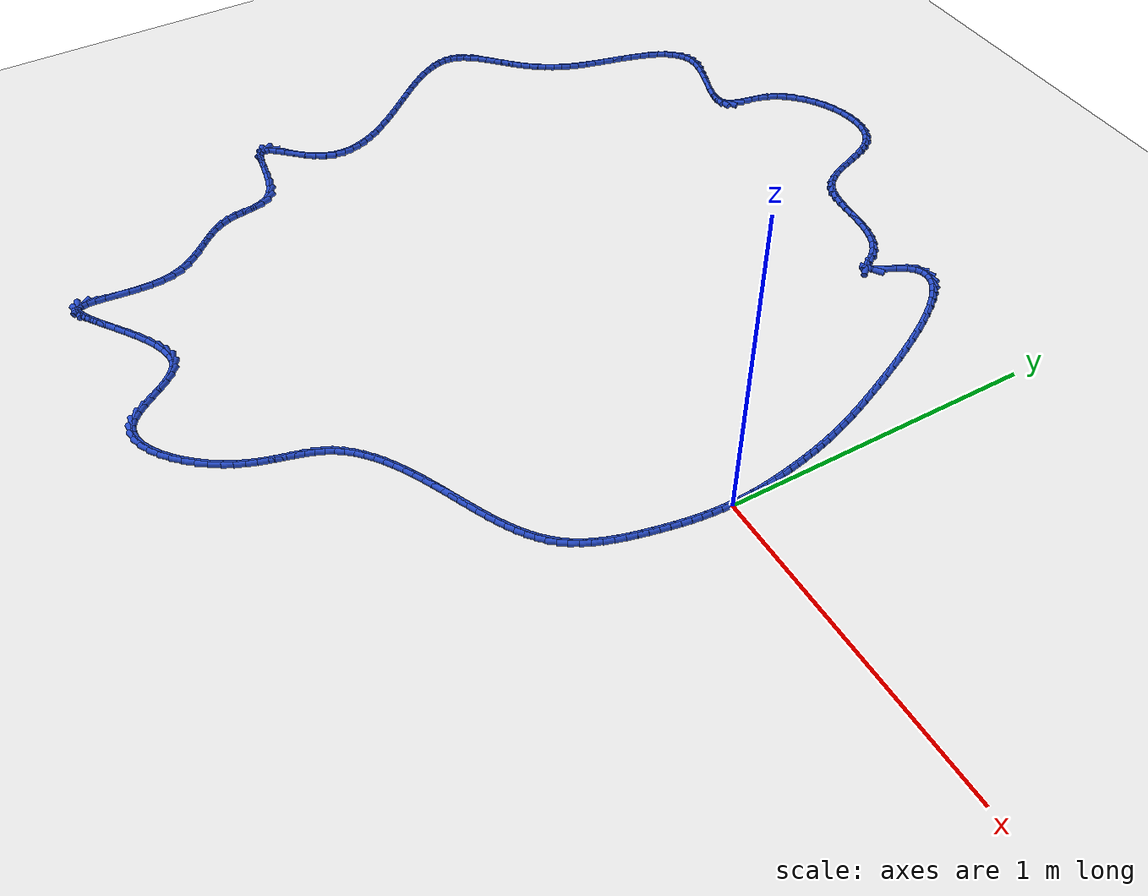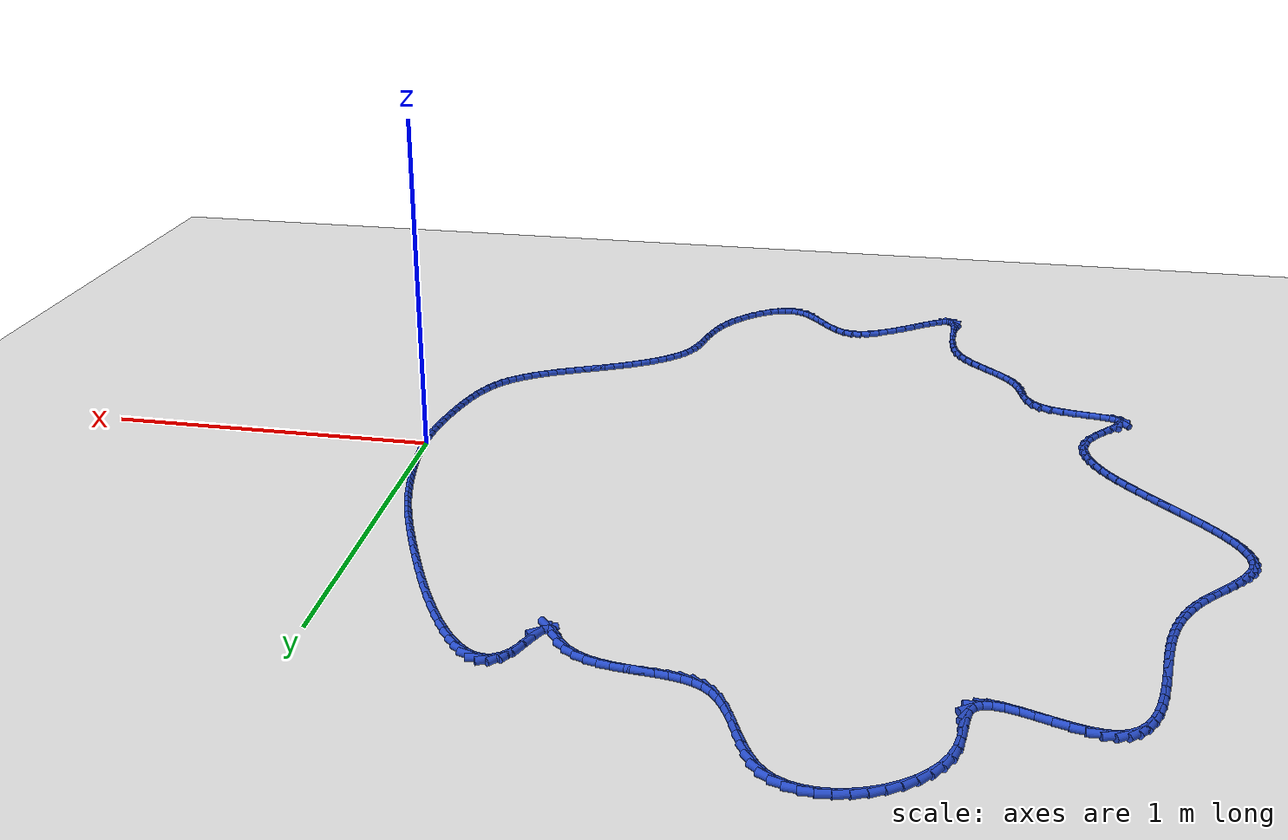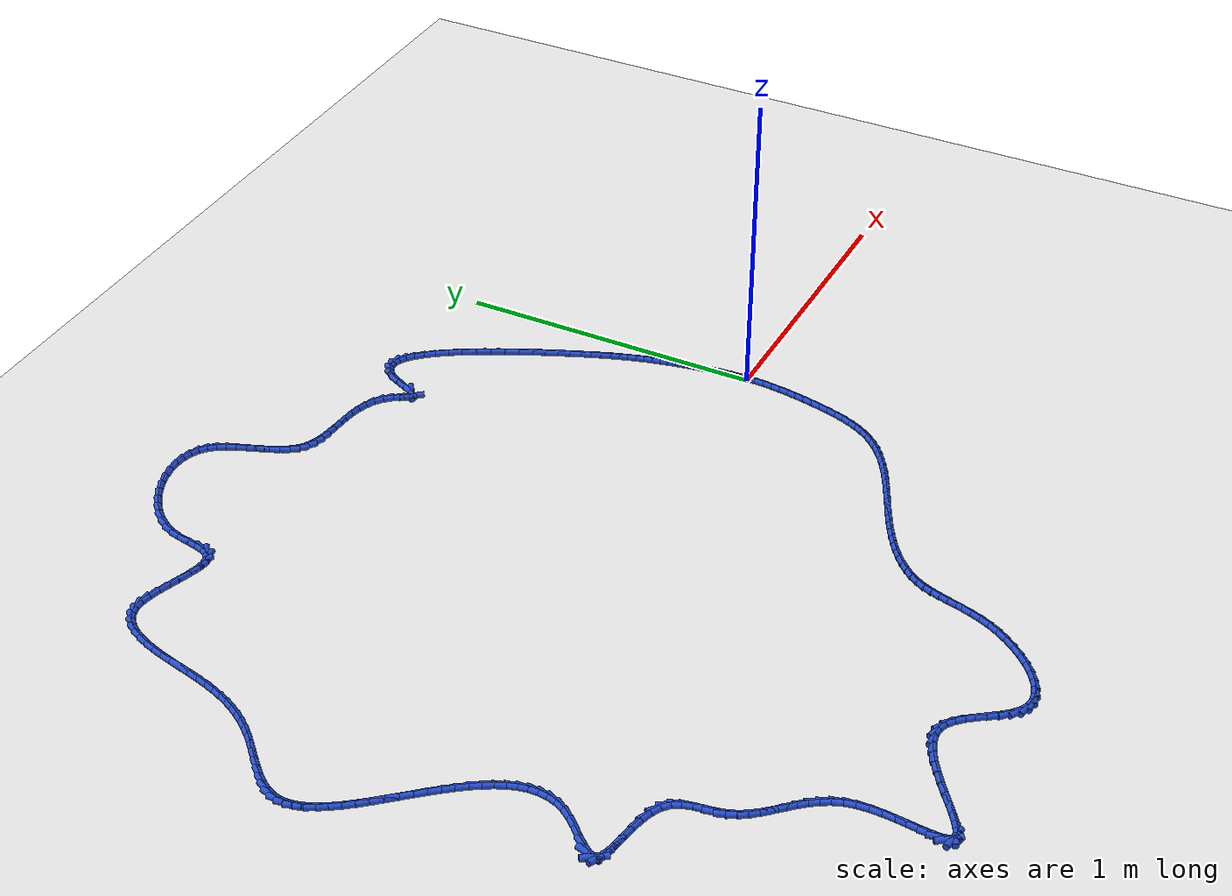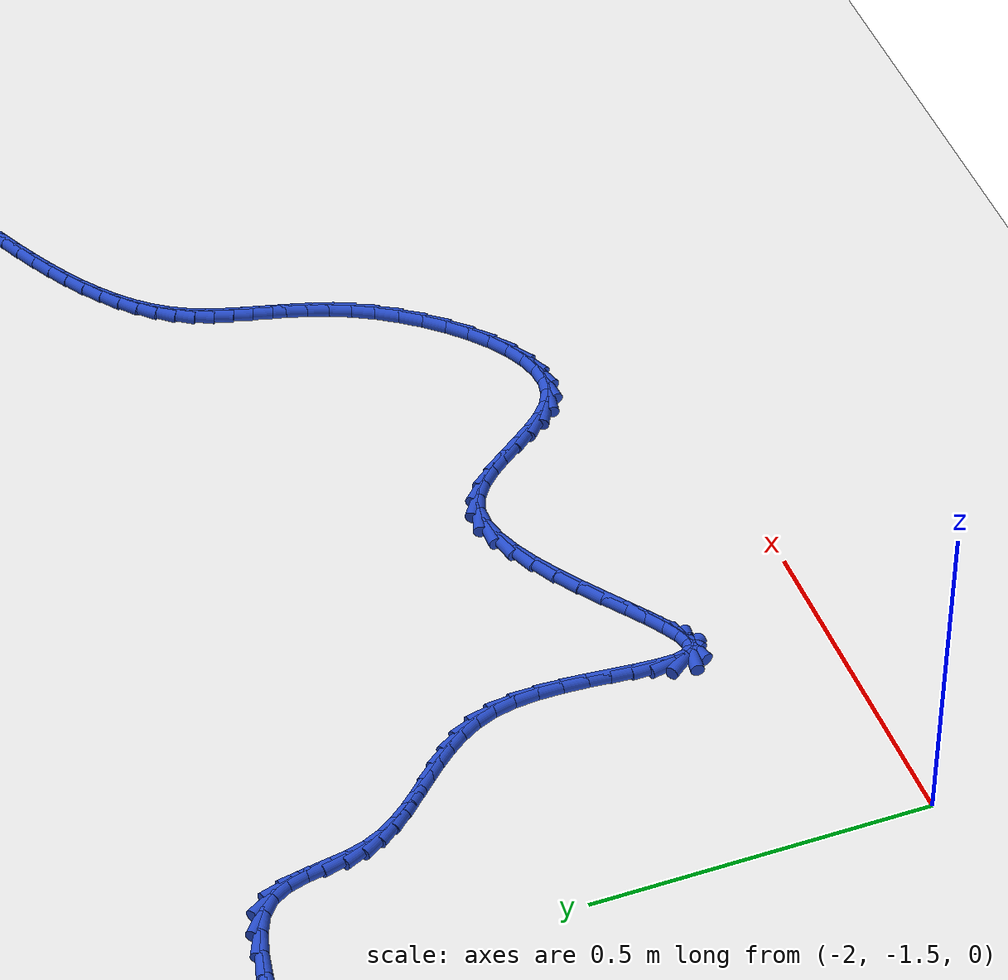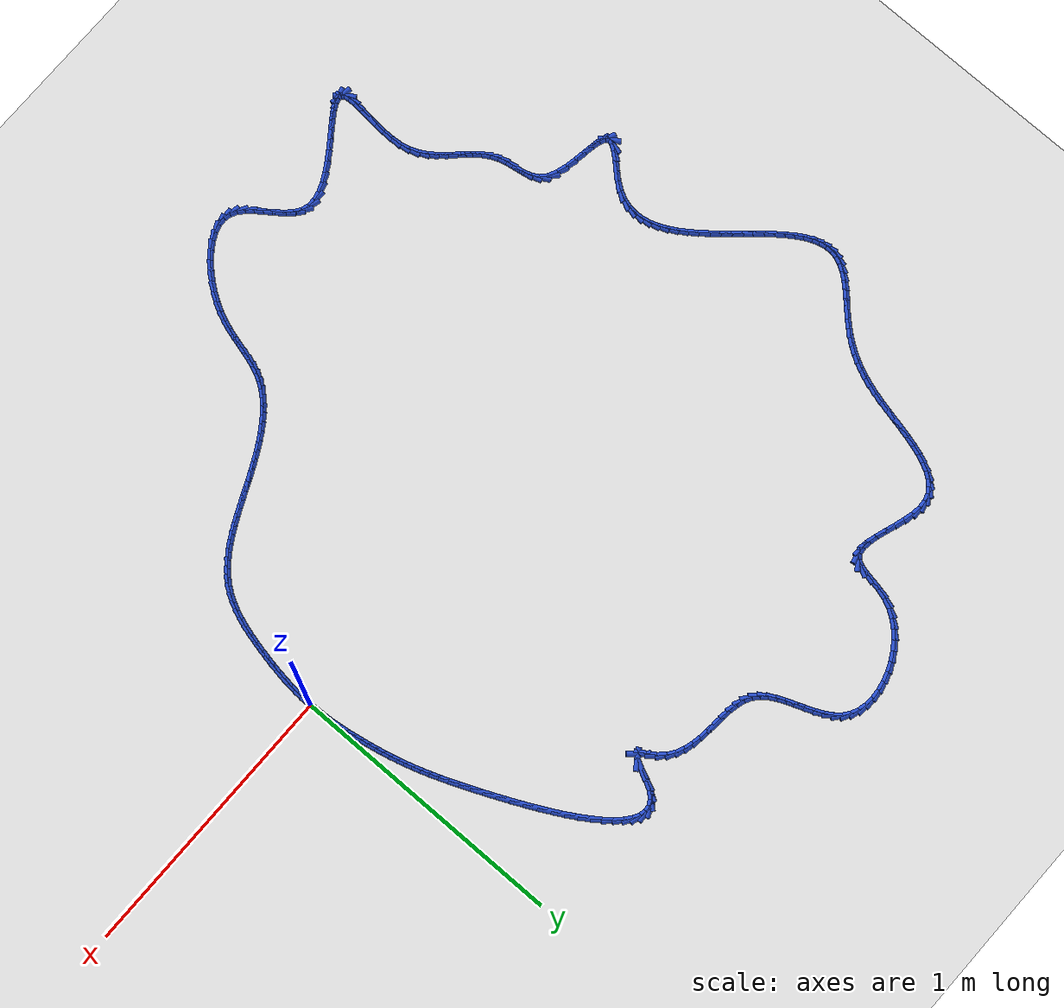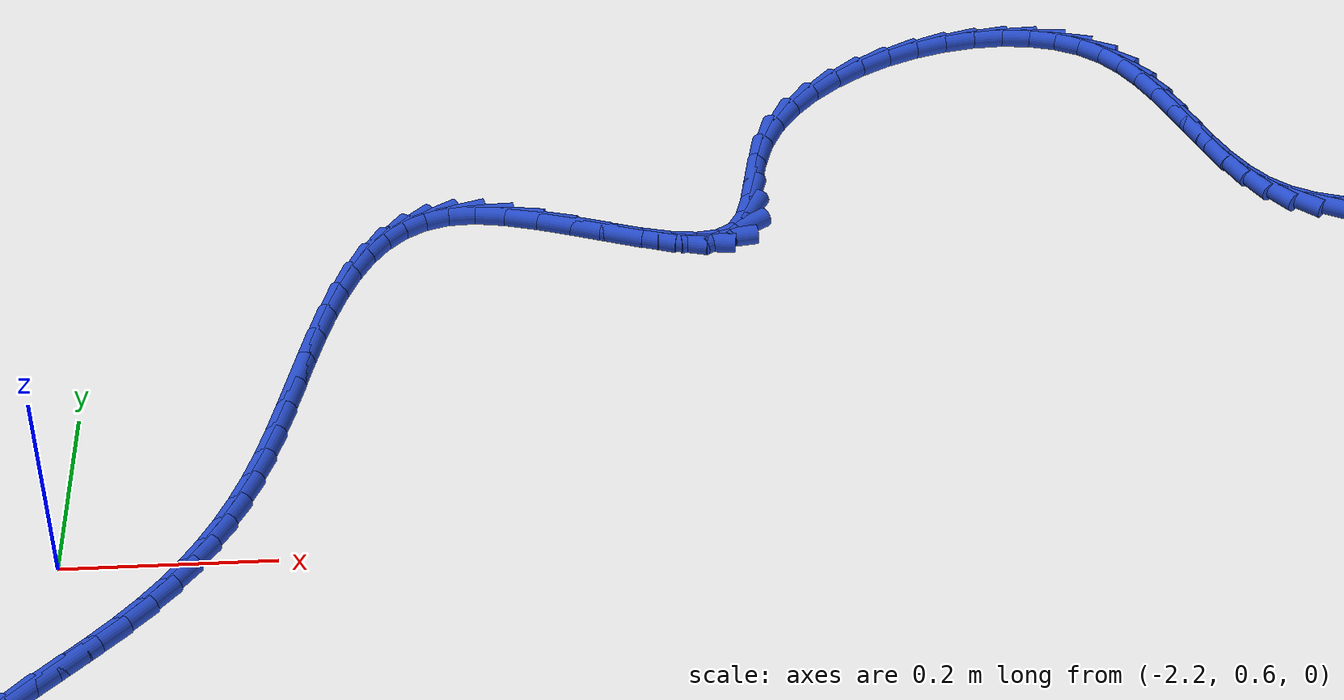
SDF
<sdf version="1.6">
 <world name="default">
  <light name="sun" type="directional">
   <pose>0 0 10 0 -0 0</pose>
   <diffuse>0.8 0.8 0.8 1</diffuse>
   <specular>0.2 0.2 0.2 1</specular>
   <attenuation>
    <range>1000</range>
    <constant>0.9</constant>
    <linear>0.01</linear>
    <quadratic>0.001</quadratic>
   </attenuation>
   <direction>-0.5 0.1 -0.9</direction>
  </light>
  <model name="ground_plane">
   <static>1</static>
   <link name="link">
    <collision name="collision">
     <geometry><plane><normal>0 0 1</normal><size>100 100</size></plane></geometry>
     <surface><friction><ode><mu>100</mu><mu2>50</mu2></ode></friction></surface>
    </collision>
    <visual name="visual">
     <cast_shadows>0</cast_shadows>
     <geometry><plane><normal>0 0 1</normal><size>100 100</size></plane></geometry>
     <material>
      <script><uri>file://media/materials/scripts/gazebo.material</uri><name>Gazebo/WhiteGlow</name></script>
     </material>
    </visual>
   </link>
  </model>
  <gravity>0 0 -9.8</gravity>
  <magnetic_field>6e-06 2.3e-05 -4.2e-05</magnetic_field>
  <atmosphere type="adiabatic"/>
  <physics name="default_physics" default="0" type="ode">
   <max_step_size>0.001</max_step_size>
   <real_time_factor>1</real_time_factor>
   <real_time_update_rate>1000</real_time_update_rate>
  </physics>
  <scene><ambient>0.4 0.4 0.4 1</ambient><background>0.7 0.7 0.7 1</background><shadows>1</shadows></scene>
  <spherical_coordinates>
   <surface_model>EARTH_WGS84</surface_model>
   <latitude_deg>0</latitude_deg>
   <longitude_deg>0</longitude_deg>
   <elevation>0</elevation>
   <heading_deg>0</heading_deg>
  </spherical_coordinates>
  <model name="line">
   <link name="link_0">
    <pose>8.673617379884035e-19 -9.71445146547012e-17 0.01 0 1.57 -1.5445140956670516</pose>
    <collision name="collision">
     <geometry><cylinder><radius>0.01</radius><length>0.08</length></cylinder></geometry>
    </collision>
    <visual name="visual">
     <material>
      <script><name>Gazebo/Blue</name><uri>file://media/materials/scripts/gazebo.material</uri></script>
     </material>
     <geometry><cylinder><radius>0.01</radius><length>0.08</length></cylinder></geometry>
    </visual>
   </link>
   <link name="link_1">
    <pose>-0.0008094161486921087 0.03078999520908032 0.01 0 1.57 -1.5099835859297035</pose>
    <collision name="collision">
     <geometry><cylinder><radius>0.01</radius><length>0.08</length></cylinder></geometry>
    </collision>
    <visual name="visual">
     <material>
      <script><name>Gazebo/Blue</name><uri>file://media/materials/scripts/gazebo.material</uri></script>
     </material>
     <geometry><cylinder><radius>0.01</radius><length>0.08</length></cylinder></geometry>
    </visual>
   </link>
   <link name="link_2">
    <pose>-0.00269315820113394 0.0617279090074299 0.01 0 1.57 -1.4797686581550331</pose>
    <collision name="collision">
     <geometry><cylinder><radius>0.01</radius><length>0.08</length></cylinder></geometry>
    </collision>
    <visual name="visual">
     <material>
      <script><name>Gazebo/Blue</name><uri>file://media/materials/scripts/gazebo.material</uri></script>
     </material>
     <geometry><cylinder><radius>0.01</radius><length>0.08</length></cylinder></geometry>
    </visual>
   </link>
   <link name="link_3">
    <pose>-0.005514027168656915 0.09263140711815195 0.01 0 1.57 -1.4533471675095304</pose>
    <collision name="collision">
     <geometry><cylinder><radius>0.01</radius><length>0.08</length></cylinder></geometry>
    </collision>
    <visual name="visual">
     <material>
      <script><name>Gazebo/Blue</name><uri>file://media/materials/scripts/gazebo.material</uri></script>
     </material>
     <geometry><cylinder><radius>0.01</radius><length>0.08</length></cylinder></geometry>
    </visual>
   </link>
   <link name="link_4">
    <pose>-0.009134824062592433 0.12331815526434962 0.01 0 1.57 -1.430300043548118</pose>
    <collision name="collision">
     <geometry><cylinder><radius>0.01</radius><length>0.08</length></cylinder></geometry>
    </collision>
    <visual name="visual">
     <material>
      <script><name>Gazebo/Blue</name><uri>file://media/materials/scripts/gazebo.material</uri></script>
     </material>
     <geometry><cylinder><radius>0.01</radius><length>0.08</length></cylinder></geometry>
    </visual>
   </link>
   <link name="link_5">
    <pose>-0.01341834989427192 0.15360581916912627 0.01 0 1.57 -1.4103016822098695</pose>
    <collision name="collision">
     <geometry><cylinder><radius>0.01</radius><length>0.08</length></cylinder></geometry>
    </collision>
    <visual name="visual">
     <material>
      <script><name>Gazebo/Blue</name><uri>file://media/materials/scripts/gazebo.material</uri></script>
     </material>
     <geometry><cylinder><radius>0.01</radius><length>0.08</length></cylinder></geometry>
    </visual>
   </link>
   <link name="link_6">
    <pose>-0.0182274056750268 0.1833120645555852 0.01 0 1.57 -1.3931137880369273</pose>
    <collision name="collision">
     <geometry><cylinder><radius>0.01</radius><length>0.08</length></cylinder></geometry>
    </collision>
    <visual name="visual">
     <material>
      <script><name>Gazebo/Blue</name><uri>file://media/materials/scripts/gazebo.material</uri></script>
     </material>
     <geometry><cylinder><radius>0.01</radius><length>0.08</length></cylinder></geometry>
    </visual>
   </link>
   <link name="link_7">
    <pose>-0.023424792416188476 0.21225455714682956 0.01 0 1.57 -1.3785484037778624</pose>
    <collision name="collision">
     <geometry><cylinder><radius>0.01</radius><length>0.08</length></cylinder></geometry>
    </collision>
    <visual name="visual">
     <material>
      <script><name>Gazebo/Blue</name><uri>file://media/materials/scripts/gazebo.material</uri></script>
     </material>
     <geometry><cylinder><radius>0.01</radius><length>0.08</length></cylinder></geometry>
    </visual>
   </link>
   <link name="link_8">
    <pose>-0.02887496337622601 0.24025413228240616 0.01 0 1.57 -1.3646404065300404</pose>
    <collision name="collision">
     <geometry><cylinder><radius>0.01</radius><length>0.08</length></cylinder></geometry>
    </collision>
    <visual name="visual">
     <material>
      <script><name>Gazebo/Blue</name><uri>file://media/materials/scripts/gazebo.material</uri></script>
     </material>
     <geometry><cylinder><radius>0.01</radius><length>0.08</length></cylinder></geometry>
    </visual>
   </link>
   <link name="link_9">
    <pose>-0.034531549262630766 0.2673027003803755 0.01 0 1.57 -1.3486882179091797</pose>
    <collision name="collision">
     <geometry><cylinder><radius>0.01</radius><length>0.08</length></cylinder></geometry>
    </collision>
    <visual name="visual">
     <material>
      <script><name>Gazebo/Blue</name><uri>file://media/materials/scripts/gazebo.material</uri></script>
     </material>
     <geometry><cylinder><radius>0.01</radius><length>0.08</length></cylinder></geometry>
    </visual>
   </link>
   <link name="link_10">
    <pose>-0.040480965479157485 0.2936469016429289 0.01 0 1.57 -1.3308129316570478</pose>
    <collision name="collision">
     <geometry><cylinder><radius>0.01</radius><length>0.08</length></cylinder></geometry>
    </collision>
    <visual name="visual">
     <material>
      <script><name>Gazebo/Blue</name><uri>file://media/materials/scripts/gazebo.material</uri></script>
     </material>
     <geometry><cylinder><radius>0.01</radius><length>0.08</length></cylinder></geometry>
    </visual>
   </link>
   <link name="link_11">
    <pose>-0.04682043675863811 0.3195541125328349 0.01 0 1.57 -1.3115223338045379</pose>
    <collision name="collision">
     <geometry><cylinder><radius>0.01</radius><length>0.08</length></cylinder></geometry>
    </collision>
    <visual name="visual">
     <material>
      <script><name>Gazebo/Blue</name><uri>file://media/materials/scripts/gazebo.material</uri></script>
     </material>
     <geometry><cylinder><radius>0.01</radius><length>0.08</length></cylinder></geometry>
    </visual>
   </link>
   <link name="link_12">
    <pose>-0.053647187833904555 0.3452917095128619 0.01 0 1.57 -1.2914332955139058</pose>
    <collision name="collision">
     <geometry><cylinder><radius>0.01</radius><length>0.08</length></cylinder></geometry>
    </collision>
    <visual name="visual">
     <material>
      <script><name>Gazebo/Blue</name><uri>file://media/materials/scripts/gazebo.material</uri></script>
     </material>
     <geometry><cylinder><radius>0.01</radius><length>0.08</length></cylinder></geometry>
    </visual>
   </link>
   <link name="link_13">
    <pose>-0.061058443437788754 0.3711270690457787 0.01 0 1.57 -1.2712066916418039</pose>
    <collision name="collision">
     <geometry><cylinder><radius>0.01</radius><length>0.08</length></cylinder></geometry>
    </collision>
    <visual name="visual">
     <material>
      <script><name>Gazebo/Blue</name><uri>file://media/materials/scripts/gazebo.material</uri></script>
     </material>
     <geometry><cylinder><radius>0.01</radius><length>0.08</length></cylinder></geometry>
    </visual>
   </link>
   <link name="link_14">
    <pose>-0.06915142830312265 0.3973275675943538 0.01 0 1.57 -1.2514760581382012</pose>
    <collision name="collision">
     <geometry><cylinder><radius>0.01</radius><length>0.08</length></cylinder></geometry>
    </collision>
    <visual name="visual">
     <material>
      <script><name>Gazebo/Blue</name><uri>file://media/materials/scripts/gazebo.material</uri></script>
     </material>
     <geometry><cylinder><radius>0.01</radius><length>0.08</length></cylinder></geometry>
    </visual>
   </link>
   <link name="link_15">
    <pose>-0.07802336716273815 0.4241605816213558 0.01 0 1.57 -1.2327857934608162</pose>
    <collision name="collision">
     <geometry><cylinder><radius>0.01</radius><length>0.08</length></cylinder></geometry>
    </collision>
    <visual name="visual">
     <material>
      <script><name>Gazebo/Blue</name><uri>file://media/materials/scripts/gazebo.material</uri></script>
     </material>
     <geometry><cylinder><radius>0.01</radius><length>0.08</length></cylinder></geometry>
    </visual>
   </link>
   <link name="link_16">
    <pose>-0.0877714847494672 0.4518934875895531 0.01 0 1.57 -1.2155506029703598</pose>
    <collision name="collision">
     <geometry><cylinder><radius>0.01</radius><length>0.08</length></cylinder></geometry>
    </collision>
    <visual name="visual">
     <material>
      <script><name>Gazebo/Blue</name><uri>file://media/materials/scripts/gazebo.material</uri></script>
     </material>
     <geometry><cylinder><radius>0.01</radius><length>0.08</length></cylinder></geometry>
    </visual>
   </link>
   <link name="link_17">
    <pose>-0.09849300579614174 0.4807936619617146 0.01 0 1.57 -1.2000403421158676</pose>
    <collision name="collision">
     <geometry><cylinder><radius>0.01</radius><length>0.08</length></cylinder></geometry>
    </collision>
    <visual name="visual">
     <material>
      <script><name>Gazebo/Blue</name><uri>file://media/materials/scripts/gazebo.material</uri></script>
     </material>
     <geometry><cylinder><radius>0.01</radius><length>0.08</length></cylinder></geometry>
    </visual>
   </link>
   <link name="link_18">
    <pose>-0.11028515503559363 0.5111284812006085 0.01 0 1.57 -1.186387157737187</pose>
    <collision name="collision">
     <geometry><cylinder><radius>0.01</radius><length>0.08</length></cylinder></geometry>
    </collision>
    <visual name="visual">
     <material>
      <script><name>Gazebo/Blue</name><uri>file://media/materials/scripts/gazebo.material</uri></script>
     </material>
     <geometry><cylinder><radius>0.01</radius><length>0.08</length></cylinder></geometry>
    </visual>
   </link>
   <link name="link_19">
    <pose>-0.12324515720065493 0.5431653217690039 0.01 0 1.57 -1.1746075333055748</pose>
    <collision name="collision">
     <geometry><cylinder><radius>0.01</radius><length>0.08</length></cylinder></geometry>
    </collision>
    <visual name="visual">
     <material>
      <script><name>Gazebo/Blue</name><uri>file://media/materials/scripts/gazebo.material</uri></script>
     </material>
     <geometry><cylinder><radius>0.01</radius><length>0.08</length></cylinder></geometry>
    </visual>
   </link>
   <link name="link_20">
    <pose>-0.13747023702415742 0.5771715601296689 0.01 0 1.57 -1.1646310487645535</pose>
    <collision name="collision">
     <geometry><cylinder><radius>0.01</radius><length>0.08</length></cylinder></geometry>
    </collision>
    <visual name="visual">
     <material>
      <script><name>Gazebo/Blue</name><uri>file://media/materials/scripts/gazebo.material</uri></script>
     </material>
     <geometry><cylinder><radius>0.01</radius><length>0.08</length></cylinder></geometry>
    </visual>
   </link>
   <link name="link_21">
    <pose>-0.15305761923893318 0.6134145727453724 0.01 0 1.57 -1.1559656001172074</pose>
    <collision name="collision">
     <geometry><cylinder><radius>0.01</radius><length>0.08</length></cylinder></geometry>
    </collision>
    <visual name="visual">
     <material>
      <script><name>Gazebo/Blue</name><uri>file://media/materials/scripts/gazebo.material</uri></script>
     </material>
     <geometry><cylinder><radius>0.01</radius><length>0.08</length></cylinder></geometry>
    </visual>
   </link>
   <link name="link_22">
    <pose>-0.17008166935689917 0.6520716298088575 0.01 0 1.57 -1.145893672674637</pose>
    <collision name="collision">
     <geometry><cylinder><radius>0.01</radius><length>0.08</length></cylinder></geometry>
    </collision>
    <visual name="visual">
     <material>
      <script><name>Gazebo/Blue</name><uri>file://media/materials/scripts/gazebo.material</uri></script>
     </material>
     <geometry><cylinder><radius>0.01</radius><length>0.08</length></cylinder></geometry>
    </visual>
   </link>
   <link name="link_23">
    <pose>-0.18845288217325235 0.692674057405455 0.01 0 1.57 -1.1331484918024868</pose>
    <collision name="collision">
     <geometry><cylinder><radius>0.01</radius><length>0.08</length></cylinder></geometry>
    </collision>
    <visual name="visual">
     <material>
      <script><name>Gazebo/Blue</name><uri>file://media/materials/scripts/gazebo.material</uri></script>
     </material>
     <geometry><cylinder><radius>0.01</radius><length>0.08</length></cylinder></geometry>
    </visual>
   </link>
   <link name="link_24">
    <pose>-0.20801024437864948 0.7344713116214832 0.01 0 1.57 -1.1173894807951799</pose>
    <collision name="collision">
     <geometry><cylinder><radius>0.01</radius><length>0.08</length></cylinder></geometry>
    </collision>
    <visual name="visual">
     <material>
      <script><name>Gazebo/Blue</name><uri>file://media/materials/scripts/gazebo.material</uri></script>
     </material>
     <geometry><cylinder><radius>0.01</radius><length>0.08</length></cylinder></geometry>
    </visual>
   </link>
   <link name="link_25">
    <pose>-0.2285924448954752 0.7767116748029821 0.01 0 1.57 -1.0980357997666819</pose>
    <collision name="collision">
     <geometry><cylinder><radius>0.01</radius><length>0.08</length></cylinder></geometry>
    </collision>
    <visual name="visual">
     <material>
      <script><name>Gazebo/Blue</name><uri>file://media/materials/scripts/gazebo.material</uri></script>
     </material>
     <geometry><cylinder><radius>0.01</radius><length>0.08</length></cylinder></geometry>
    </visual>
   </link>
   <link name="link_26">
    <pose>-0.2500381726461142 0.8186434292959915 0.01 0 1.57 -1.0741985408926187</pose>
    <collision name="collision">
     <geometry><cylinder><radius>0.01</radius><length>0.08</length></cylinder></geometry>
    </collision>
    <visual name="visual">
     <material>
      <script><name>Gazebo/Blue</name><uri>file://media/materials/scripts/gazebo.material</uri></script>
     </material>
     <geometry><cylinder><radius>0.01</radius><length>0.08</length></cylinder></geometry>
    </visual>
   </link>
   <link name="link_27">
    <pose>-0.2721861165529514 0.8595148574465521 0.01 0 1.57 -1.0445536499631238</pose>
    <collision name="collision">
     <geometry><cylinder><radius>0.01</radius><length>0.08</length></cylinder></geometry>
    </collision>
    <visual name="visual">
     <material>
      <script><name>Gazebo/Blue</name><uri>file://media/materials/scripts/gazebo.material</uri></script>
     </material>
     <geometry><cylinder><radius>0.01</radius><length>0.08</length></cylinder></geometry>
    </visual>
   </link>
   <link name="link_28">
    <pose>-0.29487496553837145 0.8985742416007035 0.01 0 1.57 -1.0071162920552923</pose>
    <collision name="collision">
     <geometry><cylinder><radius>0.01</radius><length>0.08</length></cylinder></geometry>
    </collision>
    <visual name="visual">
     <material>
      <script><name>Gazebo/Blue</name><uri>file://media/materials/scripts/gazebo.material</uri></script>
     </material>
     <geometry><cylinder><radius>0.01</radius><length>0.08</length></cylinder></geometry>
    </visual>
   </link>
   <link name="link_29">
    <pose>-0.31794340852475894 0.9350698641044857 0.01 0 1.57 -0.9588451280342456</pose>
    <collision name="collision">
     <geometry><cylinder><radius>0.01</radius><length>0.08</length></cylinder></geometry>
    </collision>
    <visual name="visual">
     <material>
      <script><name>Gazebo/Blue</name><uri>file://media/materials/scripts/gazebo.material</uri></script>
     </material>
     <geometry><cylinder><radius>0.01</radius><length>0.08</length></cylinder></geometry>
    </visual>
   </link>
   <link name="link_30">
    <pose>-0.3412301344344989 0.9682500073039392 0.01 0 1.57 -0.8949391870520805</pose>
    <collision name="collision">
     <geometry><cylinder><radius>0.01</radius><length>0.08</length></cylinder></geometry>
    </collision>
    <visual name="visual">
     <material>
      <script><name>Gazebo/Blue</name><uri>file://media/materials/scripts/gazebo.material</uri></script>
     </material>
     <geometry><cylinder><radius>0.01</radius><length>0.08</length></cylinder></geometry>
    </visual>
   </link>
   <link name="link_31">
    <pose>-0.36457383218997574 0.9973629535451036 0.01 0 1.57 -0.8075825705660558</pose>
    <collision name="collision">
     <geometry><cylinder><radius>0.01</radius><length>0.08</length></cylinder></geometry>
    </collision>
    <visual name="visual">
     <material>
      <script><name>Gazebo/Blue</name><uri>file://media/materials/scripts/gazebo.material</uri></script>
     </material>
     <geometry><cylinder><radius>0.01</radius><length>0.08</length></cylinder></geometry>
    </visual>
   </link>
   <link name="link_32">
    <pose>-0.38781319071357445 1.0216569851740191 0.01 0 1.57 -0.6838160753995134</pose>
    <collision name="collision">
     <geometry><cylinder><radius>0.01</radius><length>0.08</length></cylinder></geometry>
    </collision>
    <visual name="visual">
     <material>
      <script><name>Gazebo/Blue</name><uri>file://media/materials/scripts/gazebo.material</uri></script>
     </material>
     <geometry><cylinder><radius>0.01</radius><length>0.08</length></cylinder></geometry>
    </visual>
   </link>
   <link name="link_33">
    <pose>-0.41078689892767956 1.0403803845367259 0.01 0 1.57 -0.5028547437351969</pose>
    <collision name="collision">
     <geometry><cylinder><radius>0.01</radius><length>0.08</length></cylinder></geometry>
    </collision>
    <visual name="visual">
     <material>
      <script><name>Gazebo/Blue</name><uri>file://media/materials/scripts/gazebo.material</uri></script>
     </material>
     <geometry><cylinder><radius>0.01</radius><length>0.08</length></cylinder></geometry>
    </visual>
   </link>
   <link name="link_34">
    <pose>-0.433333645754676 1.0527814339792638 0.01 0 1.57 -0.23799572866431298</pose>
    <collision name="collision">
     <geometry><cylinder><radius>0.01</radius><length>0.08</length></cylinder></geometry>
    </collision>
    <visual name="visual">
     <material>
      <script><name>Gazebo/Blue</name><uri>file://media/materials/scripts/gazebo.material</uri></script>
     </material>
     <geometry><cylinder><radius>0.01</radius><length>0.08</length></cylinder></geometry>
    </visual>
   </link>
   <link name="link_35">
    <pose>-0.45529212011694814 1.058108415847673 0.01 0 1.57 0.1172780119326538</pose>
    <collision name="collision">
     <geometry><cylinder><radius>0.01</radius><length>0.08</length></cylinder></geometry>
    </collision>
    <visual name="visual">
     <material>
      <script><name>Gazebo/Blue</name><uri>file://media/materials/scripts/gazebo.material</uri></script>
     </material>
     <geometry><cylinder><radius>0.01</radius><length>0.08</length></cylinder></geometry>
    </visual>
   </link>
   <link name="link_36">
    <pose>-0.47650101093688124 1.0556096124879937 0.01 0 1.57 0.4995240952023879</pose>
    <collision name="collision">
     <geometry><cylinder><radius>0.01</radius><length>0.08</length></cylinder></geometry>
    </collision>
    <visual name="visual">
     <material>
      <script><name>Gazebo/Blue</name><uri>file://media/materials/scripts/gazebo.material</uri></script>
     </material>
     <geometry><cylinder><radius>0.01</radius><length>0.08</length></cylinder></geometry>
    </visual>
   </link>
   <link name="link_37">
    <pose>-0.49679900713685976 1.0445333062462656 0.01 0 1.57 0.8151571539769104</pose>
    <collision name="collision">
     <geometry><cylinder><radius>0.01</radius><length>0.08</length></cylinder></geometry>
    </collision>
    <visual name="visual">
     <material>
      <script><name>Gazebo/Blue</name><uri>file://media/materials/scripts/gazebo.material</uri></script>
     </material>
     <geometry><cylinder><radius>0.01</radius><length>0.08</length></cylinder></geometry>
    </visual>
   </link>
   <link name="link_38">
    <pose>-0.5160247976392685 1.0241277794685293 0.01 0 1.57 1.037218106697893</pose>
    <collision name="collision">
     <geometry><cylinder><radius>0.01</radius><length>0.08</length></cylinder></geometry>
    </collision>
    <visual name="visual">
     <material>
      <script><name>Gazebo/Blue</name><uri>file://media/materials/scripts/gazebo.material</uri></script>
     </material>
     <geometry><cylinder><radius>0.01</radius><length>0.08</length></cylinder></geometry>
    </visual>
   </link>
   <link name="link_39">
    <pose>-0.5340183513088653 0.9936681118715908 0.01 0 1.57 1.1435346667572042</pose>
    <collision name="collision">
     <geometry><cylinder><radius>0.01</radius><length>0.08</length></cylinder></geometry>
    </collision>
    <visual name="visual">
     <material>
      <script><name>Gazebo/Blue</name><uri>file://media/materials/scripts/gazebo.material</uri></script>
     </material>
     <geometry><cylinder><radius>0.01</radius><length>0.08</length></cylinder></geometry>
    </visual>
   </link>
   <link name="link_40">
    <pose>-0.550826154191086 0.9567531070954614 0.01 0 1.57 1.0880244593667912</pose>
    <collision name="collision">
     <geometry><cylinder><radius>0.01</radius><length>0.08</length></cylinder></geometry>
    </collision>
    <visual name="visual">
     <material>
      <script><name>Gazebo/Blue</name><uri>file://media/materials/scripts/gazebo.material</uri></script>
     </material>
     <geometry><cylinder><radius>0.01</radius><length>0.08</length></cylinder></geometry>
    </visual>
   </link>
   <link name="link_41">
    <pose>-0.5669270843009014 0.9260342950315488 0.01 0 1.57 0.5929884116296987</pose>
    <collision name="collision">
     <geometry><cylinder><radius>0.01</radius><length>0.08</length></cylinder></geometry>
    </collision>
    <visual name="visual">
     <material>
      <script><name>Gazebo/Blue</name><uri>file://media/materials/scripts/gazebo.material</uri></script>
     </material>
     <geometry><cylinder><radius>0.01</radius><length>0.08</length></cylinder></geometry>
    </visual>
   </link>
   <link name="link_42">
    <pose>-0.5828543659109934 0.915301019935335 0.01 0 1.57 -0.8402387109544881</pose>
    <collision name="collision">
     <geometry><cylinder><radius>0.01</radius><length>0.08</length></cylinder></geometry>
    </collision>
    <visual name="visual">
     <material>
      <script><name>Gazebo/Blue</name><uri>file://media/materials/scripts/gazebo.material</uri></script>
     </material>
     <geometry><cylinder><radius>0.01</radius><length>0.08</length></cylinder></geometry>
    </visual>
   </link>
   <link name="link_43">
    <pose>-0.5993373459700023 0.9336987999381102 0.01 0 1.57 -1.0144066865188532</pose>
    <collision name="collision">
     <geometry><cylinder><radius>0.01</radius><length>0.08</length></cylinder></geometry>
    </collision>
    <visual name="visual">
     <material>
      <script><name>Gazebo/Blue</name><uri>file://media/materials/scripts/gazebo.material</uri></script>
     </material>
     <geometry><cylinder><radius>0.01</radius><length>0.08</length></cylinder></geometry>
    </visual>
   </link>
   <link name="link_44">
    <pose>-0.6182116208431119 0.9640466401776853 0.01 0 1.57 -0.8342640109263174</pose>
    <collision name="collision">
     <geometry><cylinder><radius>0.01</radius><length>0.08</length></cylinder></geometry>
    </collision>
    <visual name="visual">
     <material>
      <script><name>Gazebo/Blue</name><uri>file://media/materials/scripts/gazebo.material</uri></script>
     </material>
     <geometry><cylinder><radius>0.01</radius><length>0.08</length></cylinder></geometry>
    </visual>
   </link>
   <link name="link_45">
    <pose>-0.6407668364349389 0.988921408699938 0.01 0 1.57 -0.6256301253564622</pose>
    <collision name="collision">
     <geometry><cylinder><radius>0.01</radius><length>0.08</length></cylinder></geometry>
    </collision>
    <visual name="visual">
     <material>
      <script><name>Gazebo/Blue</name><uri>file://media/materials/scripts/gazebo.material</uri></script>
     </material>
     <geometry><cylinder><radius>0.01</radius><length>0.08</length></cylinder></geometry>
    </visual>
   </link>
   <link name="link_46">
    <pose>-0.6665685115389642 1.0075616484629328 0.01 0 1.57 -0.4413386298287435</pose>
    <collision name="collision">
     <geometry><cylinder><radius>0.01</radius><length>0.08</length></cylinder></geometry>
    </collision>
    <visual name="visual">
     <material>
      <script><name>Gazebo/Blue</name><uri>file://media/materials/scripts/gazebo.material</uri></script>
     </material>
     <geometry><cylinder><radius>0.01</radius><length>0.08</length></cylinder></geometry>
    </visual>
   </link>
   <link name="link_47">
    <pose>-0.6949974177263137 1.0209919435007841 0.01 0 1.57 -0.2948852772834443</pose>
    <collision name="collision">
     <geometry><cylinder><radius>0.01</radius><length>0.08</length></cylinder></geometry>
    </collision>
    <visual name="visual">
     <material>
      <script><name>Gazebo/Blue</name><uri>file://media/materials/scripts/gazebo.material</uri></script>
     </material>
     <geometry><cylinder><radius>0.01</radius><length>0.08</length></cylinder></geometry>
    </visual>
   </link>
   <link name="link_48">
    <pose>-0.7254343265681126 1.030236877847606 0.01 0 1.57 -0.18889220728602835</pose>
    <collision name="collision">
     <geometry><cylinder><radius>0.01</radius><length>0.08</length></cylinder></geometry>
    </collision>
    <visual name="visual">
     <material>
      <script><name>Gazebo/Blue</name><uri>file://media/materials/scripts/gazebo.material</uri></script>
     </material>
     <geometry><cylinder><radius>0.01</radius><length>0.08</length></cylinder></geometry>
    </visual>
   </link>
   <link name="link_49">
    <pose>-0.7572600096354866 1.0363210355375145 0.01 0 1.57 -0.12053381596016685</pose>
    <collision name="collision">
     <geometry><cylinder><radius>0.01</radius><length>0.08</length></cylinder></geometry>
    </collision>
    <visual name="visual">
     <material>
      <script><name>Gazebo/Blue</name><uri>file://media/materials/scripts/gazebo.material</uri></script>
     </material>
     <geometry><cylinder><radius>0.01</radius><length>0.08</length></cylinder></geometry>
    </visual>
   </link>
   <link name="link_50">
    <pose>-0.7898552384995603 1.0402690006046222 0.01 0 1.57 -0.08640243113839567</pose>
    <collision name="collision">
     <geometry><cylinder><radius>0.01</radius><length>0.08</length></cylinder></geometry>
    </collision>
    <visual name="visual">
     <material>
      <script><name>Gazebo/Blue</name><uri>file://media/materials/scripts/gazebo.material</uri></script>
     </material>
     <geometry><cylinder><radius>0.01</radius><length>0.08</length></cylinder></geometry>
    </visual>
   </link>
   <link name="link_51">
    <pose>-0.8226007847314598 1.0431053570830453 0.01 0 1.57 -0.08497513101354197</pose>
    <collision name="collision">
     <geometry><cylinder><radius>0.01</radius><length>0.08</length></cylinder></geometry>
    </collision>
    <visual name="visual">
     <material>
      <script><name>Gazebo/Blue</name><uri>file://media/materials/scripts/gazebo.material</uri></script>
     </material>
     <geometry><cylinder><radius>0.01</radius><length>0.08</length></cylinder></geometry>
    </visual>
   </link>
   <link name="link_52">
    <pose>-0.8548774199023105 1.0458546890068972 0.01 0 1.57 -0.11766710511691242</pose>
    <collision name="collision">
     <geometry><cylinder><radius>0.01</radius><length>0.08</length></cylinder></geometry>
    </collision>
    <visual name="visual">
     <material>
      <script><name>Gazebo/Blue</name><uri>file://media/materials/scripts/gazebo.material</uri></script>
     </material>
     <geometry><cylinder><radius>0.01</radius><length>0.08</length></cylinder></geometry>
    </visual>
   </link>
   <link name="link_53">
    <pose>-0.8860659155832379 1.0495415804102932 0.01 0 1.57 -0.1893204956750121</pose>
    <collision name="collision">
     <geometry><cylinder><radius>0.01</radius><length>0.08</length></cylinder></geometry>
    </collision>
    <visual name="visual">
     <material>
      <script><name>Gazebo/Blue</name><uri>file://media/materials/scripts/gazebo.material</uri></script>
     </material>
     <geometry><cylinder><radius>0.01</radius><length>0.08</length></cylinder></geometry>
    </visual>
   </link>
   <link name="link_54">
    <pose>-0.915547043345367 1.0551906153273474 0.01 0 1.57 -0.30790845379074666</pose>
    <collision name="collision">
     <geometry><cylinder><radius>0.01</radius><length>0.08</length></cylinder></geometry>
    </collision>
    <visual name="visual">
     <material>
      <script><name>Gazebo/Blue</name><uri>file://media/materials/scripts/gazebo.material</uri></script>
     </material>
     <geometry><cylinder><radius>0.01</radius><length>0.08</length></cylinder></geometry>
    </visual>
   </link>
   <link name="link_55">
    <pose>-0.9427015747598236 1.0638263777921744 0.01 0 1.57 -0.48142106793282485</pose>
    <collision name="collision">
     <geometry><cylinder><radius>0.01</radius><length>0.08</length></cylinder></geometry>
    </collision>
    <visual name="visual">
     <material>
      <script><name>Gazebo/Blue</name><uri>file://media/materials/scripts/gazebo.material</uri></script>
     </material>
     <geometry><cylinder><radius>0.01</radius><length>0.08</length></cylinder></geometry>
    </visual>
   </link>
   <link name="link_56">
    <pose>-0.9669102813977329 1.076473451838889 0.01 0 1.57 -0.7046636350369208</pose>
    <collision name="collision">
     <geometry><cylinder><radius>0.01</radius><length>0.08</length></cylinder></geometry>
    </collision>
    <visual name="visual">
     <material>
      <script><name>Gazebo/Blue</name><uri>file://media/materials/scripts/gazebo.material</uri></script>
     </material>
     <geometry><cylinder><radius>0.01</radius><length>0.08</length></cylinder></geometry>
    </visual>
   </link>
   <link name="link_57">
    <pose>-0.9876092351776377 1.0940736092916912 0.01 0 1.57 -0.9095063778615197</pose>
    <collision name="collision">
     <geometry><cylinder><radius>0.01</radius><length>0.08</length></cylinder></geometry>
    </collision>
    <visual name="visual">
     <material>
      <script><name>Gazebo/Blue</name><uri>file://media/materials/scripts/gazebo.material</uri></script>
     </material>
     <geometry><cylinder><radius>0.01</radius><length>0.08</length></cylinder></geometry>
    </visual>
   </link>
   <link name="link_58">
    <pose>-1.0050001858075797 1.1164220203205089 0.01 0 1.57 -1.0529268660991993</pose>
    <collision name="collision">
     <geometry><cylinder><radius>0.01</radius><length>0.08</length></cylinder></geometry>
    </collision>
    <visual name="visual">
     <material>
      <script><name>Gazebo/Blue</name><uri>file://media/materials/scripts/gazebo.material</uri></script>
     </material>
     <geometry><cylinder><radius>0.01</radius><length>0.08</length></cylinder></geometry>
    </visual>
   </link>
   <link name="link_59">
    <pose>-1.0198442227001652 1.1424762444980283 0.01 0 1.57 -1.1434126777221763</pose>
    <collision name="collision">
     <geometry><cylinder><radius>0.01</radius><length>0.08</length></cylinder></geometry>
    </collision>
    <visual name="visual">
     <material>
      <script><name>Gazebo/Blue</name><uri>file://media/materials/scripts/gazebo.material</uri></script>
     </material>
     <geometry><cylinder><radius>0.01</radius><length>0.08</length></cylinder></geometry>
    </visual>
   </link>
   <link name="link_60">
    <pose>-1.0329151882505205 1.1711747438195312 0.01 0 1.57 -1.191450816749732</pose>
    <collision name="collision">
     <geometry><cylinder><radius>0.01</radius><length>0.08</length></cylinder></geometry>
    </collision>
    <visual name="visual">
     <material>
      <script><name>Gazebo/Blue</name><uri>file://media/materials/scripts/gazebo.material</uri></script>
     </material>
     <geometry><cylinder><radius>0.01</radius><length>0.08</length></cylinder></geometry>
    </visual>
   </link>
   <link name="link_61">
    <pose>-1.0449869248537709 1.2014559802802989 0.01 0 1.57 -1.2036434372366889</pose>
    <collision name="collision">
     <geometry><cylinder><radius>0.01</radius><length>0.08</length></cylinder></geometry>
    </collision>
    <visual name="visual">
     <material>
      <script><name>Gazebo/Blue</name><uri>file://media/materials/scripts/gazebo.material</uri></script>
     </material>
     <geometry><cylinder><radius>0.01</radius><length>0.08</length></cylinder></geometry>
    </visual>
   </link>
   <link name="link_62">
    <pose>-1.0568332749050418 1.2322584158756114 0.01 0 1.57 -1.1820571133412723</pose>
    <collision name="collision">
     <geometry><cylinder><radius>0.01</radius><length>0.08</length></cylinder></geometry>
    </collision>
    <visual name="visual">
     <material>
      <script><name>Gazebo/Blue</name><uri>file://media/materials/scripts/gazebo.material</uri></script>
     </material>
     <geometry><cylinder><radius>0.01</radius><length>0.08</length></cylinder></geometry>
    </visual>
   </link>
   <link name="link_63">
    <pose>-1.0692280807994594 1.2625205126007513 0.01 0 1.57 -1.124405647208603</pose>
    <collision name="collision">
     <geometry><cylinder><radius>0.01</radius><length>0.08</length></cylinder></geometry>
    </collision>
    <visual name="visual">
     <material>
      <script><name>Gazebo/Blue</name><uri>file://media/materials/scripts/gazebo.material</uri></script>
     </material>
     <geometry><cylinder><radius>0.01</radius><length>0.08</length></cylinder></geometry>
    </visual>
   </link>
   <link name="link_64">
    <pose>-1.0829451849321492 1.2911807324509992 0.01 0 1.57 -1.0243134010870778</pose>
    <collision name="collision">
     <geometry><cylinder><radius>0.01</radius><length>0.08</length></cylinder></geometry>
    </collision>
    <visual name="visual">
     <material>
      <script><name>Gazebo/Blue</name><uri>file://media/materials/scripts/gazebo.material</uri></script>
     </material>
     <geometry><cylinder><radius>0.01</radius><length>0.08</length></cylinder></geometry>
    </visual>
   </link>
   <link name="link_65">
    <pose>-1.0987584296982367 1.3171775374216366 0.01 0 1.57 -0.8727983603358828</pose>
    <collision name="collision">
     <geometry><cylinder><radius>0.01</radius><length>0.08</length></cylinder></geometry>
    </collision>
    <visual name="visual">
     <material>
      <script><name>Gazebo/Blue</name><uri>file://media/materials/scripts/gazebo.material</uri></script>
     </material>
     <geometry><cylinder><radius>0.01</radius><length>0.08</length></cylinder></geometry>
    </visual>
   </link>
   <link name="link_66">
    <pose>-1.1174416574928467 1.3394493895079438 0.01 0 1.57 -0.6658102244209142</pose>
    <collision name="collision">
     <geometry><cylinder><radius>0.01</radius><length>0.08</length></cylinder></geometry>
    </collision>
    <visual name="visual">
     <material>
      <script><name>Gazebo/Blue</name><uri>file://media/materials/scripts/gazebo.material</uri></script>
     </material>
     <geometry><cylinder><radius>0.01</radius><length>0.08</length></cylinder></geometry>
    </visual>
   </link>
   <link name="link_67">
    <pose>-1.1397376196013655 1.3569619121106788 0.01 0 1.57 -0.44394112524364343</pose>
    <collision name="collision">
     <geometry><cylinder><radius>0.01</radius><length>0.08</length></cylinder></geometry>
    </collision>
    <visual name="visual">
     <material>
      <script><name>Gazebo/Blue</name><uri>file://media/materials/scripts/gazebo.material</uri></script>
     </material>
     <geometry><cylinder><radius>0.01</radius><length>0.08</length></cylinder></geometry>
    </visual>
   </link>
   <link name="link_68">
    <pose>-1.1656799701055482 1.3693002007829413 0.01 0 1.57 -0.24941884112325433</pose>
    <collision name="collision">
     <geometry><cylinder><radius>0.01</radius><length>0.08</length></cylinder></geometry>
    </collision>
    <visual name="visual">
     <material>
      <script><name>Gazebo/Blue</name><uri>file://media/materials/scripts/gazebo.material</uri></script>
     </material>
     <geometry><cylinder><radius>0.01</radius><length>0.08</length></cylinder></geometry>
    </visual>
   </link>
   <link name="link_69">
    <pose>-1.1945965823613178 1.3766659259325518 0.01 0 1.57 -0.08385405090683544</pose>
    <collision name="collision">
     <geometry><cylinder><radius>0.01</radius><length>0.08</length></cylinder></geometry>
    </collision>
    <visual name="visual">
     <material>
      <script><name>Gazebo/Blue</name><uri>file://media/materials/scripts/gazebo.material</uri></script>
     </material>
     <geometry><cylinder><radius>0.01</radius><length>0.08</length></cylinder></geometry>
    </visual>
   </link>
   <link name="link_70">
    <pose>-1.2257849019149876 1.3792873399092904 0.01 0 1.57 0.05777418771580277</pose>
    <collision name="collision">
     <geometry><cylinder><radius>0.01</radius><length>0.08</length></cylinder></geometry>
    </collision>
    <visual name="visual">
     <material>
      <script><name>Gazebo/Blue</name><uri>file://media/materials/scripts/gazebo.material</uri></script>
     </material>
     <geometry><cylinder><radius>0.01</radius><length>0.08</length></cylinder></geometry>
    </visual>
   </link>
   <link name="link_71">
    <pose>-1.2585423743128736 1.3773926950629398 0.01 0 1.57 0.1818387510161537</pose>
    <collision name="collision">
     <geometry><cylinder><radius>0.01</radius><length>0.08</length></cylinder></geometry>
    </collision>
    <visual name="visual">
     <material>
      <script><name>Gazebo/Blue</name><uri>file://media/materials/scripts/gazebo.material</uri></script>
     </material>
     <geometry><cylinder><radius>0.01</radius><length>0.08</length></cylinder></geometry>
    </visual>
   </link>
   <link name="link_72">
    <pose>-1.2921664451012878 1.3712102437432785 0.01 0 1.57 0.2943208391136237</pose>
    <collision name="collision">
     <geometry><cylinder><radius>0.01</radius><length>0.08</length></cylinder></geometry>
    </collision>
    <visual name="visual">
     <material>
      <script><name>Gazebo/Blue</name><uri>file://media/materials/scripts/gazebo.material</uri></script>
     </material>
     <geometry><cylinder><radius>0.01</radius><length>0.08</length></cylinder></geometry>
    </visual>
   </link>
   <link name="link_73">
    <pose>-1.3259545598265443 1.3609682383000878 0.01 0 1.57 0.40039796299079444</pose>
    <collision name="collision">
     <geometry><cylinder><radius>0.01</radius><length>0.08</length></cylinder></geometry>
    </collision>
    <visual name="visual">
     <material>
      <script><name>Gazebo/Blue</name><uri>file://media/materials/scripts/gazebo.material</uri></script>
     </material>
     <geometry><cylinder><radius>0.01</radius><length>0.08</length></cylinder></geometry>
    </visual>
   </link>
   <link name="link_74">
    <pose>-1.3592041640349577 1.3468949310831493 0.01 0 1.57 0.5045604184586252</pose>
    <collision name="collision">
     <geometry><cylinder><radius>0.01</radius><length>0.08</length></cylinder></geometry>
    </collision>
    <visual name="visual">
     <material>
      <script><name>Gazebo/Blue</name><uri>file://media/materials/scripts/gazebo.material</uri></script>
     </material>
     <geometry><cylinder><radius>0.01</radius><length>0.08</length></cylinder></geometry>
    </visual>
   </link>
   <link name="link_75">
    <pose>-1.3912127032728399 1.3292185744422418 0.01 0 1.57 0.6108534142282459</pose>
    <collision name="collision">
     <geometry><cylinder><radius>0.01</radius><length>0.08</length></cylinder></geometry>
    </collision>
    <visual name="visual">
     <material>
      <script><name>Gazebo/Blue</name><uri>file://media/materials/scripts/gazebo.material</uri></script>
     </material>
     <geometry><cylinder><radius>0.01</radius><length>0.08</length></cylinder></geometry>
    </visual>
   </link>
   <link name="link_76">
    <pose>-1.4212776230865058 1.308167420727147 0.01 0 1.57 0.7230754647963488</pose>
    <collision name="collision">
     <geometry><cylinder><radius>0.01</radius><length>0.08</length></cylinder></geometry>
    </collision>
    <visual name="visual">
     <material>
      <script><name>Gazebo/Blue</name><uri>file://media/materials/scripts/gazebo.material</uri></script>
     </material>
     <geometry><cylinder><radius>0.01</radius><length>0.08</length></cylinder></geometry>
    </visual>
   </link>
   <link name="link_77">
    <pose>-1.4486963690222692 1.2839697222876454 0.01 0 1.57 0.84483599541593</pose>
    <collision name="collision">
     <geometry><cylinder><radius>0.01</radius><length>0.08</length></cylinder></geometry>
    </collision>
    <visual name="visual">
     <material>
      <script><name>Gazebo/Blue</name><uri>file://media/materials/scripts/gazebo.material</uri></script>
     </material>
     <geometry><cylinder><radius>0.01</radius><length>0.08</length></cylinder></geometry>
    </visual>
   </link>
   <link name="link_78">
    <pose>-1.4727663866264433 1.2568537314735175 0.01 0 1.57 0.9793628854467564</pose>
    <collision name="collision">
     <geometry><cylinder><radius>0.01</radius><length>0.08</length></cylinder></geometry>
    </collision>
    <visual name="visual">
     <material>
      <script><name>Gazebo/Blue</name><uri>file://media/materials/scripts/gazebo.material</uri></script>
     </material>
     <geometry><cylinder><radius>0.01</radius><length>0.08</length></cylinder></geometry>
    </visual>
   </link>
   <link name="link_79">
    <pose>-1.4927851214453427 1.2270477006345446 0.01 0 1.57 1.1289248704223778</pose>
    <collision name="collision">
     <geometry><cylinder><radius>0.01</radius><length>0.08</length></cylinder></geometry>
    </collision>
    <visual name="visual">
     <material>
      <script><name>Gazebo/Blue</name><uri>file://media/materials/scripts/gazebo.material</uri></script>
     </material>
     <geometry><cylinder><radius>0.01</radius><length>0.08</length></cylinder></geometry>
    </visual>
   </link>
   <link name="link_80">
    <pose>-1.50805001902528 1.1947798821205067 0.01 0 1.57 1.27980571020308</pose>
    <collision name="collision">
     <geometry><cylinder><radius>0.01</radius><length>0.08</length></cylinder></geometry>
    </collision>
    <visual name="visual">
     <material>
      <script><name>Gazebo/Blue</name><uri>file://media/materials/scripts/gazebo.material</uri></script>
     </material>
     <geometry><cylinder><radius>0.01</radius><length>0.08</length></cylinder></geometry>
    </visual>
   </link>
   <link name="link_81">
    <pose>-1.518293949381536 1.1605755210458604 0.01 0 1.57 1.3693118766113808</pose>
    <collision name="collision">
     <geometry><cylinder><radius>0.01</radius><length>0.08</length></cylinder></geometry>
    </collision>
    <visual name="visual">
     <material>
      <script><name>Gazebo/Blue</name><uri>file://media/materials/scripts/gazebo.material</uri></script>
     </material>
     <geometry><cylinder><radius>0.01</radius><length>0.08</length></cylinder></geometry>
    </visual>
   </link>
   <link name="link_82">
    <pose>-1.525285102500981 1.1263481062928011 0.01 0 1.57 1.3820144777105212</pose>
    <collision name="collision">
     <geometry><cylinder><radius>0.01</radius><length>0.08</length></cylinder></geometry>
    </collision>
    <visual name="visual">
     <material>
      <script><name>Gazebo/Blue</name><uri>file://media/materials/scripts/gazebo.material</uri></script>
     </material>
     <geometry><cylinder><radius>0.01</radius><length>0.08</length></cylinder></geometry>
    </visual>
   </link>
   <link name="link_83">
    <pose>-1.5313858724589842 1.0944164193432817 0.01 0 1.57 1.3003674564243426</pose>
    <collision name="collision">
     <geometry><cylinder><radius>0.01</radius><length>0.08</length></cylinder></geometry>
    </collision>
    <visual name="visual">
     <material>
      <script><name>Gazebo/Blue</name><uri>file://media/materials/scripts/gazebo.material</uri></script>
     </material>
     <geometry><cylinder><radius>0.01</radius><length>0.08</length></cylinder></geometry>
    </visual>
   </link>
   <link name="link_84">
    <pose>-1.5389587245398615 1.067099290249198 0.01 0 1.57 1.0605879842798105</pose>
    <collision name="collision">
     <geometry><cylinder><radius>0.01</radius><length>0.08</length></cylinder></geometry>
    </collision>
    <visual name="visual">
     <material>
      <script><name>Gazebo/Blue</name><uri>file://media/materials/scripts/gazebo.material</uri></script>
     </material>
     <geometry><cylinder><radius>0.01</radius><length>0.08</length></cylinder></geometry>
    </visual>
   </link>
   <link name="link_85">
    <pose>-1.5503661240279298 1.046715549062447 0.01 0 1.57 0.5879420920489372</pose>
    <collision name="collision">
     <geometry><cylinder><radius>0.01</radius><length>0.08</length></cylinder></geometry>
    </collision>
    <visual name="visual">
     <material>
      <script><name>Gazebo/Blue</name><uri>file://media/materials/scripts/gazebo.material</uri></script>
     </material>
     <geometry><cylinder><radius>0.01</radius><length>0.08</length></cylinder></geometry>
    </visual>
   </link>
   <link name="link_86">
    <pose>-1.567643310483354 1.0351989348190018 0.01 0 1.57 0.14391412453492888</pose>
    <collision name="collision">
     <geometry><cylinder><radius>0.01</radius><length>0.08</length></cylinder></geometry>
    </collision>
    <visual name="visual">
     <material>
      <script><name>Gazebo/Blue</name><uri>file://media/materials/scripts/gazebo.material</uri></script>
     </material>
     <geometry><cylinder><radius>0.01</radius><length>0.08</length></cylinder></geometry>
    </visual>
   </link>
   <link name="link_87">
    <pose>-1.5906060778515918 1.0318712630308802 0.01 0 1.57 -0.11201613804050921</pose>
    <collision name="collision">
     <geometry><cylinder><radius>0.01</radius><length>0.08</length></cylinder></geometry>
    </collision>
    <visual name="visual">
     <material>
      <script><name>Gazebo/Blue</name><uri>file://media/materials/scripts/gazebo.material</uri></script>
     </material>
     <geometry><cylinder><radius>0.01</radius><length>0.08</length></cylinder></geometry>
    </visual>
   </link>
   <link name="link_88">
    <pose>-1.6181483045828933 1.034969405856194 0.01 0 1.57 -0.24510492115483984</pose>
    <collision name="collision">
     <geometry><cylinder><radius>0.01</radius><length>0.08</length></cylinder></geometry>
    </collision>
    <visual name="visual">
     <material>
      <script><name>Gazebo/Blue</name><uri>file://media/materials/scripts/gazebo.material</uri></script>
     </material>
     <geometry><cylinder><radius>0.01</radius><length>0.08</length></cylinder></geometry>
    </visual>
   </link>
   <link name="link_89">
    <pose>-1.6491608718122848 1.042726708104566 0.01 0 1.57 -0.30889259791357343</pose>
    <collision name="collision">
     <geometry><cylinder><radius>0.01</radius><length>0.08</length></cylinder></geometry>
    </collision>
    <visual name="visual">
     <material>
      <script><name>Gazebo/Blue</name><uri>file://media/materials/scripts/gazebo.material</uri></script>
     </material>
     <geometry><cylinder><radius>0.01</radius><length>0.08</length></cylinder></geometry>
    </visual>
   </link>
   <link name="link_90">
    <pose>-1.6825346606747962 1.053376514585618 0.01 0 1.57 -0.32781234569823947</pose>
    <collision name="collision">
     <geometry><cylinder><radius>0.01</radius><length>0.08</length></cylinder></geometry>
    </collision>
    <visual name="visual">
     <material>
      <script><name>Gazebo/Blue</name><uri>file://media/materials/scripts/gazebo.material</uri></script>
     </material>
     <geometry><cylinder><radius>0.01</radius><length>0.08</length></cylinder></geometry>
    </visual>
   </link>
   <link name="link_91">
    <pose>-1.7171605523054536 1.0651521701089726 0.01 0 1.57 -0.30993275770164147</pose>
    <collision name="collision">
     <geometry><cylinder><radius>0.01</radius><length>0.08</length></cylinder></geometry>
    </collision>
    <visual name="visual">
     <material>
      <script><name>Gazebo/Blue</name><uri>file://media/materials/scripts/gazebo.material</uri></script>
     </material>
     <geometry><cylinder><radius>0.01</radius><length>0.08</length></cylinder></geometry>
    </visual>
   </link>
   <link name="link_92">
    <pose>-1.7519294278392865 1.0762870194842538 0.01 0 1.57 -0.25266799511501875</pose>
    <collision name="collision">
     <geometry><cylinder><radius>0.01</radius><length>0.08</length></cylinder></geometry>
    </collision>
    <visual name="visual">
     <material>
      <script><name>Gazebo/Blue</name><uri>file://media/materials/scripts/gazebo.material</uri></script>
     </material>
     <geometry><cylinder><radius>0.01</radius><length>0.08</length></cylinder></geometry>
    </visual>
   </link>
   <link name="link_93">
    <pose>-1.7857321684113225 1.0850144075210824 0.01 0 1.57 -0.14253864544142186</pose>
    <collision name="collision">
     <geometry><cylinder><radius>0.01</radius><length>0.08</length></cylinder></geometry>
    </collision>
    <visual name="visual">
     <material>
      <script><name>Gazebo/Blue</name><uri>file://media/materials/scripts/gazebo.material</uri></script>
     </material>
     <geometry><cylinder><radius>0.01</radius><length>0.08</length></cylinder></geometry>
    </visual>
   </link>
   <link name="link_94">
    <pose>-1.817459655156589 1.0895676790290814 0.01 0 1.57 0.04665474104377419</pose>
    <collision name="collision">
     <geometry><cylinder><radius>0.01</radius><length>0.08</length></cylinder></geometry>
    </collision>
    <visual name="visual">
     <material>
      <script><name>Gazebo/Blue</name><uri>file://media/materials/scripts/gazebo.material</uri></script>
     </material>
     <geometry><cylinder><radius>0.01</radius><length>0.08</length></cylinder></geometry>
    </visual>
   </link>
   <link name="link_95">
    <pose>-1.8460346643944536 1.0882335512492514 0.01 0 1.57 0.3002624172072909</pose>
    <collision name="collision">
     <geometry><cylinder><radius>0.01</radius><length>0.08</length></cylinder></geometry>
    </collision>
    <visual name="visual">
     <material>
      <script><name>Gazebo/Blue</name><uri>file://media/materials/scripts/gazebo.material</uri></script>
     </material>
     <geometry><cylinder><radius>0.01</radius><length>0.08</length></cylinder></geometry>
    </visual>
   </link>
   <link name="link_96">
    <pose>-1.871084424124321 1.080477549437988 0.01 0 1.57 0.5556231904699138</pose>
    <collision name="collision">
     <geometry><cylinder><radius>0.01</radius><length>0.08</length></cylinder></geometry>
    </collision>
    <visual name="visual">
     <material>
      <script><name>Gazebo/Blue</name><uri>file://media/materials/scripts/gazebo.material</uri></script>
     </material>
     <geometry><cylinder><radius>0.01</radius><length>0.08</length></cylinder></geometry>
    </visual>
   </link>
   <link name="link_97">
    <pose>-1.8929247969451959 1.0669175390457546 0.01 0 1.57 0.7780322936540738</pose>
    <collision name="collision">
     <geometry><cylinder><radius>0.01</radius><length>0.08</length></cylinder></geometry>
    </collision>
    <visual name="visual">
     <material>
      <script><name>Gazebo/Blue</name><uri>file://media/materials/scripts/gazebo.material</uri></script>
     </material>
     <geometry><cylinder><radius>0.01</radius><length>0.08</length></cylinder></geometry>
    </visual>
   </link>
   <link name="link_98">
    <pose>-1.911900376712923 1.048219463534349 0.01 0 1.57 0.9532601589361375</pose>
    <collision name="collision">
     <geometry><cylinder><radius>0.01</radius><length>0.08</length></cylinder></geometry>
    </collision>
    <visual name="visual">
     <material>
      <script><name>Gazebo/Blue</name><uri>file://media/materials/scripts/gazebo.material</uri></script>
     </material>
     <geometry><cylinder><radius>0.01</radius><length>0.08</length></cylinder></geometry>
    </visual>
   </link>
   <link name="link_99">
    <pose>-1.9283557572833476 1.025049266365569 0.01 0 1.57 1.0839502350235661</pose>
    <collision name="collision">
     <geometry><cylinder><radius>0.01</radius><length>0.08</length></cylinder></geometry>
    </collision>
    <visual name="visual">
     <material>
      <script><name>Gazebo/Blue</name><uri>file://media/materials/scripts/gazebo.material</uri></script>
     </material>
     <geometry><cylinder><radius>0.01</radius><length>0.08</length></cylinder></geometry>
    </visual>
   </link>
   <link name="link_100">
    <pose>-1.942635532512316 0.9980728910012117 0.01 0 1.57 1.1788327812139152</pose>
    <collision name="collision">
     <geometry><cylinder><radius>0.01</radius><length>0.08</length></cylinder></geometry>
    </collision>
    <visual name="visual">
     <material>
      <script><name>Gazebo/Blue</name><uri>file://media/materials/scripts/gazebo.material</uri></script>
     </material>
     <geometry><cylinder><radius>0.01</radius><length>0.08</length></cylinder></geometry>
    </visual>
   </link>
   <link name="link_101">
    <pose>-1.955084296255673 0.9679562809030746 0.01 0 1.57 1.246322306157445</pose>
    <collision name="collision">
     <geometry><cylinder><radius>0.01</radius><length>0.08</length></cylinder></geometry>
    </collision>
    <visual name="visual">
     <material>
      <script><name>Gazebo/Blue</name><uri>file://media/materials/scripts/gazebo.material</uri></script>
     </material>
     <geometry><cylinder><radius>0.01</radius><length>0.08</length></cylinder></geometry>
    </visual>
   </link>
   <link name="link_102">
    <pose>-1.9660466423692637 0.935365379532956 0.01 0 1.57 1.2927072455384423</pose>
    <collision name="collision">
     <geometry><cylinder><radius>0.01</radius><length>0.08</length></cylinder></geometry>
    </collision>
    <visual name="visual">
     <material>
      <script><name>Gazebo/Blue</name><uri>file://media/materials/scripts/gazebo.material</uri></script>
     </material>
     <geometry><cylinder><radius>0.01</radius><length>0.08</length></cylinder></geometry>
    </visual>
   </link>
   <link name="link_103">
    <pose>-1.975867164708934 0.9009661303526519 0.01 0 1.57 1.3221698426986555</pose>
    <collision name="collision">
     <geometry><cylinder><radius>0.01</radius><length>0.08</length></cylinder></geometry>
    </collision>
    <visual name="visual">
     <material>
      <script><name>Gazebo/Blue</name><uri>file://media/materials/scripts/gazebo.material</uri></script>
     </material>
     <geometry><cylinder><radius>0.01</radius><length>0.08</length></cylinder></geometry>
    </visual>
   </link>
   <link name="link_104">
    <pose>-1.9848904571305297 0.8654244768239611 0.01 0 1.57 1.3371867595751015</pose>
    <collision name="collision">
     <geometry><cylinder><radius>0.01</radius><length>0.08</length></cylinder></geometry>
    </collision>
    <visual name="visual">
     <material>
      <script><name>Gazebo/Blue</name><uri>file://media/materials/scripts/gazebo.material</uri></script>
     </material>
     <geometry><cylinder><radius>0.01</radius><length>0.08</length></cylinder></geometry>
    </visual>
   </link>
   <link name="link_105">
    <pose>-1.9934611134898959 0.8294063624086807 0.01 0 1.57 1.3388503457237175</pose>
    <collision name="collision">
     <geometry><cylinder><radius>0.01</radius><length>0.08</length></cylinder></geometry>
    </collision>
    <visual name="visual">
     <material>
      <script><name>Gazebo/Blue</name><uri>file://media/materials/scripts/gazebo.material</uri></script>
     </material>
     <geometry><cylinder><radius>0.01</radius><length>0.08</length></cylinder></geometry>
    </visual>
   </link>
   <link name="link_106">
    <pose>-2.001923727642877 0.7935777305686079 0.01 0 1.57 1.3270057661451578</pose>
    <collision name="collision">
     <geometry><cylinder><radius>0.01</radius><length>0.08</length></cylinder></geometry>
    </collision>
    <visual name="visual">
     <material>
      <script><name>Gazebo/Blue</name><uri>file://media/materials/scripts/gazebo.material</uri></script>
     </material>
     <geometry><cylinder><radius>0.01</radius><length>0.08</length></cylinder></geometry>
    </visual>
   </link>
   <link name="link_107">
    <pose>-2.0106228934453196 0.7586045247655403 0.01 0 1.57 1.300180234724623</pose>
    <collision name="collision">
     <geometry><cylinder><radius>0.01</radius><length>0.08</length></cylinder></geometry>
    </collision>
    <visual name="visual">
     <material>
      <script><name>Gazebo/Blue</name><uri>file://media/materials/scripts/gazebo.material</uri></script>
     </material>
     <geometry><cylinder><radius>0.01</radius><length>0.08</length></cylinder></geometry>
    </visual>
   </link>
   <link name="link_108">
    <pose>-2.019903180853616 0.7251525883459156 0.01 0 1.57 1.258384236811561</pose>
    <collision name="collision">
     <geometry><cylinder><radius>0.01</radius><length>0.08</length></cylinder></geometry>
    </collision>
    <visual name="visual">
     <material>
      <script><name>Gazebo/Blue</name><uri>file://media/materials/scripts/gazebo.material</uri></script>
     </material>
     <geometry><cylinder><radius>0.01</radius><length>0.08</length></cylinder></geometry>
    </visual>
   </link>
   <link name="link_109">
    <pose>-2.0300633547259195 0.6936958860451435 0.01 0 1.57 1.2089016913327766</pose>
    <collision name="collision">
     <geometry><cylinder><radius>0.01</radius><length>0.08</length></cylinder></geometry>
    </collision>
    <visual name="visual">
     <material>
      <script><name>Gazebo/Blue</name><uri>file://media/materials/scripts/gazebo.material</uri></script>
     </material>
     <geometry><cylinder><radius>0.01</radius><length>0.08</length></cylinder></geometry>
    </visual>
   </link>
   <link name="link_110">
    <pose>-2.04126098740377 0.6641169238960533 0.01 0 1.57 1.154032345566911</pose>
    <collision name="collision">
     <geometry><cylinder><radius>0.01</radius><length>0.08</length></cylinder></geometry>
    </collision>
    <visual name="visual">
     <material>
      <script><name>Gazebo/Blue</name><uri>file://media/materials/scripts/gazebo.material</uri></script>
     </material>
     <geometry><cylinder><radius>0.01</radius><length>0.08</length></cylinder></geometry>
    </visual>
   </link>
   <link name="link_111">
    <pose>-2.053626532942096 0.6361846088045469 0.01 0 1.57 1.0949889726988837</pose>
    <collision name="collision">
     <geometry><cylinder><radius>0.01</radius><length>0.08</length></cylinder></geometry>
    </collision>
    <visual name="visual">
     <material>
      <script><name>Gazebo/Blue</name><uri>file://media/materials/scripts/gazebo.material</uri></script>
     </material>
     <geometry><cylinder><radius>0.01</radius><length>0.08</length></cylinder></geometry>
    </visual>
   </link>
   <link name="link_112">
    <pose>-2.067290445395825 0.6096678476765265 0.01 0 1.57 1.0334780994776314</pose>
    <collision name="collision">
     <geometry><cylinder><radius>0.01</radius><length>0.08</length></cylinder></geometry>
    </collision>
    <visual name="visual">
     <material>
      <script><name>Gazebo/Blue</name><uri>file://media/materials/scripts/gazebo.material</uri></script>
     </material>
     <geometry><cylinder><radius>0.01</radius><length>0.08</length></cylinder></geometry>
    </visual>
   </link>
   <link name="link_113">
    <pose>-2.082383178819885 0.5843355474178942 0.01 0 1.57 0.9715376107698199</pose>
    <collision name="collision">
     <geometry><cylinder><radius>0.01</radius><length>0.08</length></cylinder></geometry>
    </collision>
    <visual name="visual">
     <material>
      <script><name>Gazebo/Blue</name><uri>file://media/materials/scripts/gazebo.material</uri></script>
     </material>
     <geometry><cylinder><radius>0.01</radius><length>0.08</length></cylinder></geometry>
    </visual>
   </link>
   <link name="link_114">
    <pose>-2.099035187269203 0.5599566149345513 0.01 0 1.57 0.911279566574505</pose>
    <collision name="collision">
     <geometry><cylinder><radius>0.01</radius><length>0.08</length></cylinder></geometry>
    </collision>
    <visual name="visual">
     <material>
      <script><name>Gazebo/Blue</name><uri>file://media/materials/scripts/gazebo.material</uri></script>
     </material>
     <geometry><cylinder><radius>0.01</radius><length>0.08</length></cylinder></geometry>
    </visual>
   </link>
   <link name="link_115">
    <pose>-2.117376924798707 0.5362999571324003 0.01 0 1.57 0.854609754963089</pose>
    <collision name="collision">
     <geometry><cylinder><radius>0.01</radius><length>0.08</length></cylinder></geometry>
    </collision>
    <visual name="visual">
     <material>
      <script><name>Gazebo/Blue</name><uri>file://media/materials/scripts/gazebo.material</uri></script>
     </material>
     <geometry><cylinder><radius>0.01</radius><length>0.08</length></cylinder></geometry>
    </visual>
   </link>
   <link name="link_116">
    <pose>-2.1375388454633253 0.5131344809173431 0.01 0 1.57 0.8042039459244709</pose>
    <collision name="collision">
     <geometry><cylinder><radius>0.01</radius><length>0.08</length></cylinder></geometry>
    </collision>
    <visual name="visual">
     <material>
      <script><name>Gazebo/Blue</name><uri>file://media/materials/scripts/gazebo.material</uri></script>
     </material>
     <geometry><cylinder><radius>0.01</radius><length>0.08</length></cylinder></geometry>
    </visual>
   </link>
   <link name="link_117">
    <pose>-2.1595913467042447 0.4902365519960121 0.01 0 1.57 0.7726773357318931</pose>
    <collision name="collision">
     <geometry><cylinder><radius>0.01</radius><length>0.08</length></cylinder></geometry>
    </collision>
    <visual name="visual">
     <material>
      <script><name>Gazebo/Blue</name><uri>file://media/materials/scripts/gazebo.material</uri></script>
     </material>
     <geometry><cylinder><radius>0.01</radius><length>0.08</length></cylinder></geometry>
    </visual>
   </link>
   <link name="link_118">
    <pose>-2.1829510403541015 0.46746373373623074 0.01 0 1.57 0.7651176140945208</pose>
    <collision name="collision">
     <geometry><cylinder><radius>0.01</radius><length>0.08</length></cylinder></geometry>
    </collision>
    <visual name="visual">
     <material>
      <script><name>Gazebo/Blue</name><uri>file://media/materials/scripts/gazebo.material</uri></script>
     </material>
     <geometry><cylinder><radius>0.01</radius><length>0.08</length></cylinder></geometry>
    </visual>
   </link>
   <link name="link_119">
    <pose>-2.2066328975224243 0.4447234717408062 0.01 0 1.57 0.7807354393282722</pose>
    <collision name="collision">
     <geometry><cylinder><radius>0.01</radius><length>0.08</length></cylinder></geometry>
    </collision>
    <visual name="visual">
     <material>
      <script><name>Gazebo/Blue</name><uri>file://media/materials/scripts/gazebo.material</uri></script>
     </material>
     <geometry><cylinder><radius>0.01</radius><length>0.08</length></cylinder></geometry>
    </visual>
   </link>
   <link name="link_120">
    <pose>-2.2296460452880202 0.4219239374187126 0.01 0 1.57 0.821430380301404</pose>
    <collision name="collision">
     <geometry><cylinder><radius>0.01</radius><length>0.08</length></cylinder></geometry>
    </collision>
    <visual name="visual">
     <material>
      <script><name>Gazebo/Blue</name><uri>file://media/materials/scripts/gazebo.material</uri></script>
     </material>
     <geometry><cylinder><radius>0.01</radius><length>0.08</length></cylinder></geometry>
    </visual>
   </link>
   <link name="link_121">
    <pose>-2.2509996107296977 0.398973302178924 0.01 0 1.57 0.8921698240808598</pose>
    <collision name="collision">
     <geometry><cylinder><radius>0.01</radius><length>0.08</length></cylinder></geometry>
    </collision>
    <visual name="visual">
     <material>
      <script><name>Gazebo/Blue</name><uri>file://media/materials/scripts/gazebo.material</uri></script>
     </material>
     <geometry><cylinder><radius>0.01</radius><length>0.08</length></cylinder></geometry>
    </visual>
   </link>
   <link name="link_122">
    <pose>-2.2697027209262637 0.3757797374304147 0.01 0 1.57 1.001372926383263</pose>
    <collision name="collision">
     <geometry><cylinder><radius>0.01</radius><length>0.08</length></cylinder></geometry>
    </collision>
    <visual name="visual">
     <material>
      <script><name>Gazebo/Blue</name><uri>file://media/materials/scripts/gazebo.material</uri></script>
     </material>
     <geometry><cylinder><radius>0.01</radius><length>0.08</length></cylinder></geometry>
    </visual>
   </link>
   <link name="link_123">
    <pose>-2.284764502956528 0.35225141458215914 0.01 0 1.57 1.160163358918053</pose>
    <collision name="collision">
     <geometry><cylinder><radius>0.01</radius><length>0.08</length></cylinder></geometry>
    </collision>
    <visual name="visual">
     <material>
      <script><name>Gazebo/Blue</name><uri>file://media/materials/scripts/gazebo.material</uri></script>
     </material>
     <geometry><cylinder><radius>0.01</radius><length>0.08</length></cylinder></geometry>
    </visual>
   </link>
   <link name="link_124">
    <pose>-2.295194086019718 0.3282965052130225 0.01 0 1.57 1.3664664401117363</pose>
    <collision name="collision">
     <geometry><cylinder><radius>0.01</radius><length>0.08</length></cylinder></geometry>
    </collision>
    <visual name="visual">
     <material>
      <script><name>Gazebo/Blue</name><uri>file://media/materials/scripts/gazebo.material</uri></script>
     </material>
     <geometry><cylinder><radius>0.01</radius><length>0.08</length></cylinder></geometry>
    </visual>
   </link>
   <link name="link_125">
    <pose>-2.3002611669103374 0.3038440580111148 0.01 0 1.57 -1.5689652550183486</pose>
    <collision name="collision">
     <geometry><cylinder><radius>0.01</radius><length>0.08</length></cylinder></geometry>
    </collision>
    <visual name="visual">
     <material>
      <script><name>Gazebo/Blue</name><uri>file://media/materials/scripts/gazebo.material</uri></script>
     </material>
     <geometry><cylinder><radius>0.01</radius><length>0.08</length></cylinder></geometry>
    </visual>
   </link>
   <link name="link_126">
    <pose>-2.300215495511063 0.2789016451485018 0.01 0 1.57 -1.388697299877915</pose>
    <collision name="collision">
     <geometry><cylinder><radius>0.01</radius><length>0.08</length></cylinder></geometry>
    </collision>
    <visual name="visual">
     <material>
      <script><name>Gazebo/Blue</name><uri>file://media/materials/scripts/gazebo.material</uri></script>
     </material>
     <geometry><cylinder><radius>0.01</radius><length>0.08</length></cylinder></geometry>
    </visual>
   </link>
   <link name="link_127">
    <pose>-2.2955371986942152 0.2534952969849416 0.01 0 1.57 -1.2415412085038042</pose>
    <collision name="collision">
     <geometry><cylinder><radius>0.01</radius><length>0.08</length></cylinder></geometry>
    </collision>
    <visual name="visual">
     <material>
      <script><name>Gazebo/Blue</name><uri>file://media/materials/scripts/gazebo.material</uri></script>
     </material>
     <geometry><cylinder><radius>0.01</radius><length>0.08</length></cylinder></geometry>
    </visual>
   </link>
   <link name="link_128">
    <pose>-2.286706403332114 0.2276510438801922 0.01 0 1.57 -1.1263693836089619</pose>
    <collision name="collision">
     <geometry><cylinder><radius>0.01</radius><length>0.08</length></cylinder></geometry>
    </collision>
    <visual name="visual">
     <material>
      <script><name>Gazebo/Blue</name><uri>file://media/materials/scripts/gazebo.material</uri></script>
     </material>
     <geometry><cylinder><radius>0.01</radius><length>0.08</length></cylinder></geometry>
    </visual>
   </link>
   <link name="link_129">
    <pose>-2.2742032362970797 0.20139491619401156 0.01 0 1.57 -1.03841263760796</pose>
    <collision name="collision">
     <geometry><cylinder><radius>0.01</radius><length>0.08</length></cylinder></geometry>
    </collision>
    <visual name="visual">
     <material>
      <script><name>Gazebo/Blue</name><uri>file://media/materials/scripts/gazebo.material</uri></script>
     </material>
     <geometry><cylinder><radius>0.01</radius><length>0.08</length></cylinder></geometry>
    </visual>
   </link>
   <link name="link_130">
    <pose>-2.2585078244614323 0.17475294428615773 0.01 0 1.57 -0.9724476873907664</pose>
    <collision name="collision">
     <geometry><cylinder><radius>0.01</radius><length>0.08</length></cylinder></geometry>
    </collision>
    <visual name="visual">
     <material>
      <script><name>Gazebo/Blue</name><uri>file://media/materials/scripts/gazebo.material</uri></script>
     </material>
     <geometry><cylinder><radius>0.01</radius><length>0.08</length></cylinder></geometry>
    </visual>
   </link>
   <link name="link_131">
    <pose>-2.240100294697492 0.14775115851638884 0.01 0 1.57 -0.9240757221711742</pose>
    <collision name="collision">
     <geometry><cylinder><radius>0.01</radius><length>0.08</length></cylinder></geometry>
    </collision>
    <visual name="visual">
     <material>
      <script><name>Gazebo/Blue</name><uri>file://media/materials/scripts/gazebo.material</uri></script>
     </material>
     <geometry><cylinder><radius>0.01</radius><length>0.08</length></cylinder></geometry>
    </visual>
   </link>
   <link name="link_132">
    <pose>-2.2194607738775796 0.12041558924446272 0.01 0 1.57 -0.8899810792300304</pose>
    <collision name="collision">
     <geometry><cylinder><radius>0.01</radius><length>0.08</length></cylinder></geometry>
    </collision>
    <visual name="visual">
     <material>
      <script><name>Gazebo/Blue</name><uri>file://media/materials/scripts/gazebo.material</uri></script>
     </material>
     <geometry><cylinder><radius>0.01</radius><length>0.08</length></cylinder></geometry>
    </visual>
   </link>
   <link name="link_133">
    <pose>-2.1970693888740134 0.09277226683013745 0.01 0 1.57 -0.8678253272322163</pose>
    <collision name="collision">
     <geometry><cylinder><radius>0.01</radius><length>0.08</length></cylinder></geometry>
    </collision>
    <visual name="visual">
     <material>
      <script><name>Gazebo/Blue</name><uri>file://media/materials/scripts/gazebo.material</uri></script>
     </material>
     <geometry><cylinder><radius>0.01</radius><length>0.08</length></cylinder></geometry>
    </visual>
   </link>
   <link name="link_134">
    <pose>-2.173406266559116 0.06484722163317158 0.01 0 1.57 -0.8560691337073291</pose>
    <collision name="collision">
     <geometry><cylinder><radius>0.01</radius><length>0.08</length></cylinder></geometry>
    </collision>
    <visual name="visual">
     <material>
      <script><name>Gazebo/Blue</name><uri>file://media/materials/scripts/gazebo.material</uri></script>
     </material>
     <geometry><cylinder><radius>0.01</radius><length>0.08</length></cylinder></geometry>
    </visual>
   </link>
   <link name="link_135">
    <pose>-2.148951533805205 0.03666648401332215 0.01 0 1.57 -0.8538209944956001</pose>
    <collision name="collision">
     <geometry><cylinder><radius>0.01</radius><length>0.08</length></cylinder></geometry>
    </collision>
    <visual name="visual">
     <material>
      <script><name>Gazebo/Blue</name><uri>file://media/materials/scripts/gazebo.material</uri></script>
     </material>
     <geometry><cylinder><radius>0.01</radius><length>0.08</length></cylinder></geometry>
    </visual>
   </link>
   <link name="link_136">
    <pose>-2.1241853174846024 0.008256084330347219 0.01 0 1.57 -0.8607361774679425</pose>
    <collision name="collision">
     <geometry><cylinder><radius>0.01</radius><length>0.08</length></cylinder></geometry>
    </collision>
    <visual name="visual">
     <material>
      <script><name>Gazebo/Blue</name><uri>file://media/materials/scripts/gazebo.material</uri></script>
     </material>
     <geometry><cylinder><radius>0.01</radius><length>0.08</length></cylinder></geometry>
    </visual>
   </link>
   <link name="link_137">
    <pose>-2.099587744469628 -0.020357947055993905 0.01 0 1.57 -0.8769652375034089</pose>
    <collision name="collision">
     <geometry><cylinder><radius>0.01</radius><length>0.08</length></cylinder></geometry>
    </collision>
    <visual name="visual">
     <material>
      <script><name>Gazebo/Blue</name><uri>file://media/materials/scripts/gazebo.material</uri></script>
     </material>
     <geometry><cylinder><radius>0.01</radius><length>0.08</length></cylinder></geometry>
    </visual>
   </link>
   <link name="link_138">
    <pose>-2.075638941632601 -0.04914957978594491 0.01 0 1.57 -0.9031455912797525</pose>
    <collision name="collision">
     <geometry><cylinder><radius>0.01</radius><length>0.08</length></cylinder></geometry>
    </collision>
    <visual name="visual">
     <material>
      <script><name>Gazebo/Blue</name><uri>file://media/materials/scripts/gazebo.material</uri></script>
     </material>
     <geometry><cylinder><radius>0.01</radius><length>0.08</length></cylinder></geometry>
    </visual>
   </link>
   <link name="link_139">
    <pose>-2.0528190358458427 -0.07809278349974609 0.01 0 1.57 -0.9404273449143901</pose>
    <collision name="collision">
     <geometry><cylinder><radius>0.01</radius><length>0.08</length></cylinder></geometry>
    </collision>
    <visual name="visual">
     <material>
      <script><name>Gazebo/Blue</name><uri>file://media/materials/scripts/gazebo.material</uri></script>
     </material>
     <geometry><cylinder><radius>0.01</radius><length>0.08</length></cylinder></geometry>
    </visual>
   </link>
   <link name="link_140">
    <pose>-2.0316081539816726 -0.10716152783764023 0.01 0 1.57 -0.99051786147918</pose>
    <collision name="collision">
     <geometry><cylinder><radius>0.01</radius><length>0.08</length></cylinder></geometry>
    </collision>
    <visual name="visual">
     <material>
      <script><name>Gazebo/Blue</name><uri>file://media/materials/scripts/gazebo.material</uri></script>
     </material>
     <geometry><cylinder><radius>0.01</radius><length>0.08</length></cylinder></geometry>
    </visual>
   </link>
   <link name="link_141">
    <pose>-2.0124864229124104 -0.13632978243987026 0.01 0 1.57 -1.0557098295075826</pose>
    <collision name="collision">
     <geometry><cylinder><radius>0.01</radius><length>0.08</length></cylinder></geometry>
    </collision>
    <visual name="visual">
     <material>
      <script><name>Gazebo/Blue</name><uri>file://media/materials/scripts/gazebo.material</uri></script>
     </material>
     <geometry><cylinder><radius>0.01</radius><length>0.08</length></cylinder></geometry>
    </visual>
   </link>
   <link name="link_142">
    <pose>-1.995933969510377 -0.16557151694667638 0.01 0 1.57 -1.1388118481738803</pose>
    <collision name="collision">
     <geometry><cylinder><radius>0.01</radius><length>0.08</length></cylinder></geometry>
    </collision>
    <visual name="visual">
     <material>
      <script><name>Gazebo/Blue</name><uri>file://media/materials/scripts/gazebo.material</uri></script>
     </material>
     <geometry><cylinder><radius>0.01</radius><length>0.08</length></cylinder></geometry>
    </visual>
   </link>
   <link name="link_143">
    <pose>-1.982430920647892 -0.19486070099830227 0.01 0 1.57 -1.242815863957498</pose>
    <collision name="collision">
     <geometry><cylinder><radius>0.01</radius><length>0.08</length></cylinder></geometry>
    </collision>
    <visual name="visual">
     <material>
      <script><name>Gazebo/Blue</name><uri>file://media/materials/scripts/gazebo.material</uri></script>
     </material>
     <geometry><cylinder><radius>0.01</radius><length>0.08</length></cylinder></geometry>
    </visual>
   </link>
   <link name="link_144">
    <pose>-1.9724574031972768 -0.22417130423498827 0.01 0 1.57 -1.3700347168763618</pose>
    <collision name="collision">
     <geometry><cylinder><radius>0.01</radius><length>0.08</length></cylinder></geometry>
    </collision>
    <visual name="visual">
     <material>
      <script><name>Gazebo/Blue</name><uri>file://media/materials/scripts/gazebo.material</uri></script>
     </material>
     <geometry><cylinder><radius>0.01</radius><length>0.08</length></cylinder></geometry>
    </visual>
   </link>
   <link name="link_145">
    <pose>-1.9664935440308495 -0.253477296296978 0.01 0 1.57 -1.520486761899401</pose>
    <collision name="collision">
     <geometry><cylinder><radius>0.01</radius><length>0.08</length></cylinder></geometry>
    </collision>
    <visual name="visual">
     <material>
      <script><name>Gazebo/Blue</name><uri>file://media/materials/scripts/gazebo.material</uri></script>
     </material>
     <geometry><cylinder><radius>0.01</radius><length>0.08</length></cylinder></geometry>
    </visual>
   </link>
   <link name="link_146">
    <pose>-1.9650194700209314 -0.2827526468245118 0.01 0 1.57 1.451718414804494</pose>
    <collision name="collision">
     <geometry><cylinder><radius>0.01</radius><length>0.08</length></cylinder></geometry>
    </collision>
    <visual name="visual">
     <material>
      <script><name>Gazebo/Blue</name><uri>file://media/materials/scripts/gazebo.material</uri></script>
     </material>
     <geometry><cylinder><radius>0.01</radius><length>0.08</length></cylinder></geometry>
    </visual>
   </link>
   <link name="link_147">
    <pose>-1.9685153080398425 -0.31197132545783324 0.01 0 1.57 1.2728944397398632</pose>
    <collision name="collision">
     <geometry><cylinder><radius>0.01</radius><length>0.08</length></cylinder></geometry>
    </collision>
    <visual name="visual">
     <material>
      <script><name>Gazebo/Blue</name><uri>file://media/materials/scripts/gazebo.material</uri></script>
     </material>
     <geometry><cylinder><radius>0.01</radius><length>0.08</length></cylinder></geometry>
    </visual>
   </link>
   <link name="link_148">
    <pose>-1.9774611849599029 -0.3411073018371828 0.01 0 1.57 1.0972102495821443</pose>
    <collision name="collision">
     <geometry><cylinder><radius>0.01</radius><length>0.08</length></cylinder></geometry>
    </collision>
    <visual name="visual">
     <material>
      <script><name>Gazebo/Blue</name><uri>file://media/materials/scripts/gazebo.material</uri></script>
     </material>
     <geometry><cylinder><radius>0.01</radius><length>0.08</length></cylinder></geometry>
    </visual>
   </link>
   <link name="link_149">
    <pose>-1.9923372276534335 -0.37013454560280407 0.01 0 1.57 0.9420355888676528</pose>
    <collision name="collision">
     <geometry><cylinder><radius>0.01</radius><length>0.08</length></cylinder></geometry>
    </collision>
    <visual name="visual">
     <material>
      <script><name>Gazebo/Blue</name><uri>file://media/materials/scripts/gazebo.material</uri></script>
     </material>
     <geometry><cylinder><radius>0.01</radius><length>0.08</length></cylinder></geometry>
    </visual>
   </link>
   <link name="link_150">
    <pose>-2.0133035834759885 -0.3989654394112665 0.01 0 1.57 0.8488577502482019</pose>
    <collision name="collision">
     <geometry><cylinder><radius>0.01</radius><length>0.08</length></cylinder></geometry>
    </collision>
    <visual name="visual">
     <material>
      <script><name>Gazebo/Blue</name><uri>file://media/materials/scripts/gazebo.material</uri></script>
     </material>
     <geometry><cylinder><radius>0.01</radius><length>0.08</length></cylinder></geometry>
    </visual>
   </link>
   <link name="link_151">
    <pose>-2.038014589541808 -0.4270300685021886 0.01 0 1.57 0.8159530457453256</pose>
    <collision name="collision">
     <geometry><cylinder><radius>0.01</radius><length>0.08</length></cylinder></geometry>
    </collision>
    <visual name="visual">
     <material>
      <script><name>Gazebo/Blue</name><uri>file://media/materials/scripts/gazebo.material</uri></script>
     </material>
     <geometry><cylinder><radius>0.01</radius><length>0.08</length></cylinder></geometry>
    </visual>
   </link>
   <link name="link_152">
    <pose>-2.0629438392142037 -0.45353125842418385 0.01 0 1.57 0.840531120354488</pose>
    <collision name="collision">
     <geometry><cylinder><radius>0.01</radius><length>0.08</length></cylinder></geometry>
    </collision>
    <visual name="visual">
     <material>
      <script><name>Gazebo/Blue</name><uri>file://media/materials/scripts/gazebo.material</uri></script>
     </material>
     <geometry><cylinder><radius>0.01</radius><length>0.08</length></cylinder></geometry>
    </visual>
   </link>
   <link name="link_153">
    <pose>-2.0845580035074542 -0.47767050236996456 0.01 0 1.57 0.9574966306443287</pose>
    <collision name="collision">
     <geometry><cylinder><radius>0.01</radius><length>0.08</length></cylinder></geometry>
    </collision>
    <visual name="visual">
     <material>
      <script><name>Gazebo/Blue</name><uri>file://media/materials/scripts/gazebo.material</uri></script>
     </material>
     <geometry><cylinder><radius>0.01</radius><length>0.08</length></cylinder></geometry>
    </visual>
   </link>
   <link name="link_154">
    <pose>-2.0993237534358387 -0.4986492935322454 0.01 0 1.57 1.3186942539630504</pose>
    <collision name="collision">
     <geometry><cylinder><radius>0.01</radius><length>0.08</length></cylinder></geometry>
    </collision>
    <visual name="visual">
     <material>
      <script><name>Gazebo/Blue</name><uri>file://media/materials/scripts/gazebo.material</uri></script>
     </material>
     <geometry><cylinder><radius>0.01</radius><length>0.08</length></cylinder></geometry>
    </visual>
   </link>
   <link name="link_155">
    <pose>-2.1037077600136347 -0.5156691251037389 0.01 0 1.57 -0.9749293887276882</pose>
    <collision name="collision">
     <geometry><cylinder><radius>0.01</radius><length>0.08</length></cylinder></geometry>
    </collision>
    <visual name="visual">
     <material>
      <script><name>Gazebo/Blue</name><uri>file://media/materials/scripts/gazebo.material</uri></script>
     </material>
     <geometry><cylinder><radius>0.01</radius><length>0.08</length></cylinder></geometry>
    </visual>
   </link>
   <link name="link_156">
    <pose>-2.0951701759245176 -0.5282598281232559 0.01 0 1.57 -0.4289145983045296</pose>
    <collision name="collision">
     <geometry><cylinder><radius>0.01</radius><length>0.08</length></cylinder></geometry>
    </collision>
    <visual name="visual">
     <material>
      <script><name>Gazebo/Blue</name><uri>file://media/materials/scripts/gazebo.material</uri></script>
     </material>
     <geometry><cylinder><radius>0.01</radius><length>0.08</length></cylinder></geometry>
    </visual>
   </link>
   <link name="link_157">
    <pose>-2.075339138659145 -0.5373287196932574 0.01 0 1.57 -0.23550298773128087</pose>
    <collision name="collision">
     <geometry><cylinder><radius>0.01</radius><length>0.08</length></cylinder></geometry>
    </collision>
    <visual name="visual">
     <material>
      <script><name>Gazebo/Blue</name><uri>file://media/materials/scripts/gazebo.material</uri></script>
     </material>
     <geometry><cylinder><radius>0.01</radius><length>0.08</length></cylinder></geometry>
    </visual>
   </link>
   <link name="link_158">
    <pose>-2.046935642287342 -0.5441442973852062 0.01 0 1.57 -0.1686006774829085</pose>
    <collision name="collision">
     <geometry><cylinder><radius>0.01</radius><length>0.08</length></cylinder></geometry>
    </collision>
    <visual name="visual">
     <material>
      <script><name>Gazebo/Blue</name><uri>file://media/materials/scripts/gazebo.material</uri></script>
     </material>
     <geometry><cylinder><radius>0.01</radius><length>0.08</length></cylinder></geometry>
    </visual>
   </link>
   <link name="link_159">
    <pose>-2.0126806850613526 -0.5499750601528203 0.01 0 1.57 -0.16211632006032978</pose>
    <collision name="collision">
     <geometry><cylinder><radius>0.01</radius><length>0.08</length></cylinder></geometry>
    </collision>
    <visual name="visual">
     <material>
      <script><name>Gazebo/Blue</name><uri>file://media/materials/scripts/gazebo.material</uri></script>
     </material>
     <geometry><cylinder><radius>0.01</radius><length>0.08</length></cylinder></geometry>
    </visual>
   </link>
   <link name="link_160">
    <pose>-1.9752952652334195 -0.5560895069498182 0.01 0 1.57 -0.2001328488171359</pose>
    <collision name="collision">
     <geometry><cylinder><radius>0.01</radius><length>0.08</length></cylinder></geometry>
    </collision>
    <visual name="visual">
     <material>
      <script><name>Gazebo/Blue</name><uri>file://media/materials/scripts/gazebo.material</uri></script>
     </material>
     <geometry><cylinder><radius>0.01</radius><length>0.08</length></cylinder></geometry>
    </visual>
   </link>
   <link name="link_161">
    <pose>-1.937500381055785 -0.5637561367299182 0.01 0 1.57 -0.2873746212448334</pose>
    <collision name="collision">
     <geometry><cylinder><radius>0.01</radius><length>0.08</length></cylinder></geometry>
    </collision>
    <visual name="visual">
     <material>
      <script><name>Gazebo/Blue</name><uri>file://media/materials/scripts/gazebo.material</uri></script>
     </material>
     <geometry><cylinder><radius>0.01</radius><length>0.08</length></cylinder></geometry>
    </visual>
   </link>
   <link name="link_162">
    <pose>-1.902017030780694 -0.5742434484468386 0.01 0 1.57 -0.44645448244465274</pose>
    <collision name="collision">
     <geometry><cylinder><radius>0.01</radius><length>0.08</length></cylinder></geometry>
    </collision>
    <visual name="visual">
     <material>
      <script><name>Gazebo/Blue</name><uri>file://media/materials/scripts/gazebo.material</uri></script>
     </material>
     <geometry><cylinder><radius>0.01</radius><length>0.08</length></cylinder></geometry>
    </visual>
   </link>
   <link name="link_163">
    <pose>-1.8715662126603883 -0.5888199410542981 0.01 0 1.57 -0.7196946822047133</pose>
    <collision name="collision">
     <geometry><cylinder><radius>0.01</radius><length>0.08</length></cylinder></geometry>
    </collision>
    <visual name="visual">
     <material>
      <script><name>Gazebo/Blue</name><uri>file://media/materials/scripts/gazebo.material</uri></script>
     </material>
     <geometry><cylinder><radius>0.01</radius><length>0.08</length></cylinder></geometry>
    </visual>
   </link>
   <link name="link_164">
    <pose>-1.8488414227174939 -0.6087388525869437 0.01 0 1.57 -1.0589328805668148</pose>
    <collision name="collision">
     <geometry><cylinder><radius>0.01</radius><length>0.08</length></cylinder></geometry>
    </collision>
    <visual name="visual">
     <material>
      <script><name>Gazebo/Blue</name><uri>file://media/materials/scripts/gazebo.material</uri></script>
     </material>
     <geometry><cylinder><radius>0.01</radius><length>0.08</length></cylinder></geometry>
    </visual>
   </link>
   <link name="link_165">
    <pose>-1.8345610604036895 -0.6341574448860713 0.01 0 1.57 -1.29183750167751</pose>
    <collision name="collision">
     <geometry><cylinder><radius>0.01</radius><length>0.08</length></cylinder></geometry>
    </collision>
    <visual name="visual">
     <material>
      <script><name>Gazebo/Blue</name><uri>file://media/materials/scripts/gazebo.material</uri></script>
     </material>
     <geometry><cylinder><radius>0.01</radius><length>0.08</length></cylinder></geometry>
    </visual>
   </link>
   <link name="link_166">
    <pose>-1.8261790280334127 -0.663421518420238 0.01 0 1.57 -1.4018710597784083</pose>
    <collision name="collision">
     <geometry><cylinder><radius>0.01</radius><length>0.08</length></cylinder></geometry>
    </collision>
    <visual name="visual">
     <material>
      <script><name>Gazebo/Blue</name><uri>file://media/materials/scripts/gazebo.material</uri></script>
     </material>
     <geometry><cylinder><radius>0.01</radius><length>0.08</length></cylinder></geometry>
    </visual>
   </link>
   <link name="link_167">
    <pose>-1.82084325431449 -0.6947070896618341 0.01 0 1.57 -1.4089127735226457</pose>
    <collision name="collision">
     <geometry><cylinder><radius>0.01</radius><length>0.08</length></cylinder></geometry>
    </collision>
    <visual name="visual">
     <material>
      <script><name>Gazebo/Blue</name><uri>file://media/materials/scripts/gazebo.material</uri></script>
     </material>
     <geometry><cylinder><radius>0.01</radius><length>0.08</length></cylinder></geometry>
    </visual>
   </link>
   <link name="link_168">
    <pose>-1.8157016679547486 -0.7261901750832467 0.01 0 1.57 -1.315742328848679</pose>
    <collision name="collision">
     <geometry><cylinder><radius>0.01</radius><length>0.08</length></cylinder></geometry>
    </collision>
    <visual name="visual">
     <material>
      <script><name>Gazebo/Blue</name><uri>file://media/materials/scripts/gazebo.material</uri></script>
     </material>
     <geometry><cylinder><radius>0.01</radius><length>0.08</length></cylinder></geometry>
    </visual>
   </link>
   <link name="link_169">
    <pose>-1.8079149228495186 -0.7560550630736539 0.01 0 1.57 -1.1548129138747654</pose>
    <collision name="collision">
     <geometry><cylinder><radius>0.01</radius><length>0.08</length></cylinder></geometry>
    </collision>
    <visual name="visual">
     <material>
      <script><name>Gazebo/Blue</name><uri>file://media/materials/scripts/gazebo.material</uri></script>
     </material>
     <geometry><cylinder><radius>0.01</radius><length>0.08</length></cylinder></geometry>
    </visual>
   </link>
   <link name="link_170">
    <pose>-1.7958828355289826 -0.7832915507977091 0.01 0 1.57 -1.0136051006716646</pose>
    <collision name="collision">
     <geometry><cylinder><radius>0.01</radius><length>0.08</length></cylinder></geometry>
    </collision>
    <visual name="visual">
     <material>
      <script><name>Gazebo/Blue</name><uri>file://media/materials/scripts/gazebo.material</uri></script>
     </material>
     <geometry><cylinder><radius>0.01</radius><length>0.08</length></cylinder></geometry>
    </visual>
   </link>
   <link name="link_171">
    <pose>-1.7802650736017644 -0.8083584353913055 0.01 0 1.57 -0.9093242878773161</pose>
    <collision name="collision">
     <geometry><cylinder><radius>0.01</radius><length>0.08</length></cylinder></geometry>
    </collision>
    <visual name="visual">
     <material>
      <script><name>Gazebo/Blue</name><uri>file://media/materials/scripts/gazebo.material</uri></script>
     </material>
     <geometry><cylinder><radius>0.01</radius><length>0.08</length></cylinder></geometry>
    </visual>
   </link>
   <link name="link_172">
    <pose>-1.761961570062916 -0.8318706967800428 0.01 0 1.57 -0.8435414990073047</pose>
    <collision name="collision">
     <geometry><cylinder><radius>0.01</radius><length>0.08</length></cylinder></geometry>
    </collision>
    <visual name="visual">
     <material>
      <script><name>Gazebo/Blue</name><uri>file://media/materials/scripts/gazebo.material</uri></script>
     </material>
     <geometry><cylinder><radius>0.01</radius><length>0.08</length></cylinder></geometry>
    </visual>
   </link>
   <link name="link_173">
    <pose>-1.7418722579074926 -0.8544433148895199 0.01 0 1.57 -0.8148360808402384</pose>
    <collision name="collision">
     <geometry><cylinder><radius>0.01</radius><length>0.08</length></cylinder></geometry>
    </collision>
    <visual name="visual">
     <material>
      <script><name>Gazebo/Blue</name><uri>file://media/materials/scripts/gazebo.material</uri></script>
     </material>
     <geometry><cylinder><radius>0.01</radius><length>0.08</length></cylinder></geometry>
    </visual>
   </link>
   <link name="link_174">
    <pose>-1.7208970701305444 -0.8766912696453371 0.01 0 1.57 -0.8216389008223832</pose>
    <collision name="collision">
     <geometry><cylinder><radius>0.01</radius><length>0.08</length></cylinder></geometry>
    </collision>
    <visual name="visual">
     <material>
      <script><name>Gazebo/Blue</name><uri>file://media/materials/scripts/gazebo.material</uri></script>
     </material>
     <geometry><cylinder><radius>0.01</radius><length>0.08</length></cylinder></geometry>
    </visual>
   </link>
   <link name="link_175">
    <pose>-1.6999359397271256 -0.8992295409730926 0.01 0 1.57 -0.863335458177522</pose>
    <collision name="collision">
     <geometry><cylinder><radius>0.01</radius><length>0.08</length></cylinder></geometry>
    </collision>
    <visual name="visual">
     <material>
      <script><name>Gazebo/Blue</name><uri>file://media/materials/scripts/gazebo.material</uri></script>
     </material>
     <geometry><cylinder><radius>0.01</radius><length>0.08</length></cylinder></geometry>
    </visual>
   </link>
   <link name="link_176">
    <pose>-1.679888799692289 -0.9226731087983876 0.01 0 1.57 -0.9399674762414553</pose>
    <collision name="collision">
     <geometry><cylinder><radius>0.01</radius><length>0.08</length></cylinder></geometry>
    </collision>
    <visual name="visual">
     <material>
      <script><name>Gazebo/Blue</name><uri>file://media/materials/scripts/gazebo.material</uri></script>
     </material>
     <geometry><cylinder><radius>0.01</radius><length>0.08</length></cylinder></geometry>
    </visual>
   </link>
   <link name="link_177">
    <pose>-1.661655583021088 -0.9476369530468198 0.01 0 1.57 -1.05070046222411</pose>
    <collision name="collision">
     <geometry><cylinder><radius>0.01</radius><length>0.08</length></cylinder></geometry>
    </collision>
    <visual name="visual">
     <material>
      <script><name>Gazebo/Blue</name><uri>file://media/materials/scripts/gazebo.material</uri></script>
     </material>
     <geometry><cylinder><radius>0.01</radius><length>0.08</length></cylinder></geometry>
    </visual>
   </link>
   <link name="link_178">
    <pose>-1.6461362227085745 -0.9747360536439909 0.01 0 1.57 -1.1912770122000576</pose>
    <collision name="collision">
     <geometry><cylinder><radius>0.01</radius><length>0.08</length></cylinder></geometry>
    </collision>
    <visual name="visual">
     <material>
      <script><name>Gazebo/Blue</name><uri>file://media/materials/scripts/gazebo.material</uri></script>
     </material>
     <geometry><cylinder><radius>0.01</radius><length>0.08</length></cylinder></geometry>
    </visual>
   </link>
   <link name="link_179">
    <pose>-1.6342306517498029 -1.0045853905154982 0.01 0 1.57 -1.3500986380280786</pose>
    <collision name="collision">
     <geometry><cylinder><radius>0.01</radius><length>0.08</length></cylinder></geometry>
    </collision>
    <visual name="visual">
     <material>
      <script><name>Gazebo/Blue</name><uri>file://media/materials/scripts/gazebo.material</uri></script>
     </material>
     <geometry><cylinder><radius>0.01</radius><length>0.08</length></cylinder></geometry>
    </visual>
   </link>
   <link name="link_180">
    <pose>-1.6267897383473868 -1.0377516188153155 0.01 0 1.57 -1.4845023686465435</pose>
    <collision name="collision">
     <geometry><cylinder><radius>0.01</radius><length>0.08</length></cylinder></geometry>
    </collision>
    <visual name="visual">
     <material>
      <script><name>Gazebo/Blue</name><uri>file://media/materials/scripts/gazebo.material</uri></script>
     </material>
     <geometry><cylinder><radius>0.01</radius><length>0.08</length></cylinder></geometry>
    </visual>
   </link>
   <link name="link_181">
    <pose>-1.623669382170305 -1.0738214317985442 0.01 0 1.57 1.5673406079146939</pose>
    <collision name="collision">
     <geometry><cylinder><radius>0.01</radius><length>0.08</length></cylinder></geometry>
    </collision>
    <visual name="visual">
     <material>
      <script><name>Gazebo/Blue</name><uri>file://media/materials/scripts/gazebo.material</uri></script>
     </material>
     <geometry><cylinder><radius>0.01</radius><length>0.08</length></cylinder></geometry>
    </visual>
   </link>
   <link name="link_182">
    <pose>-1.6237994837938237 -1.111469490028252 0.01 0 1.57 1.5107830044740125</pose>
    <collision name="collision">
     <geometry><cylinder><radius>0.01</radius><length>0.08</length></cylinder></geometry>
    </collision>
    <visual name="visual">
     <material>
      <script><name>Gazebo/Blue</name><uri>file://media/materials/scripts/gazebo.material</uri></script>
     </material>
     <geometry><cylinder><radius>0.01</radius><length>0.08</length></cylinder></geometry>
    </visual>
   </link>
   <link name="link_183">
    <pose>-1.6260746952079554 -1.1493357371198158 0.01 0 1.57 1.4807740166514165</pose>
    <collision name="collision">
     <geometry><cylinder><radius>0.01</radius><length>0.08</length></cylinder></geometry>
    </collision>
    <visual name="visual">
     <material>
      <script><name>Gazebo/Blue</name><uri>file://media/materials/scripts/gazebo.material</uri></script>
     </material>
     <geometry><cylinder><radius>0.01</radius><length>0.08</length></cylinder></geometry>
    </visual>
   </link>
   <link name="link_184">
    <pose>-1.629389668402714 -1.18606011668861 0.01 0 1.57 1.4761311531900103</pose>
    <collision name="collision">
     <geometry><cylinder><radius>0.01</radius><length>0.08</length></cylinder></geometry>
    </collision>
    <visual name="visual">
     <material>
      <script><name>Gazebo/Blue</name><uri>file://media/materials/scripts/gazebo.material</uri></script>
     </material>
     <geometry><cylinder><radius>0.01</radius><length>0.08</length></cylinder></geometry>
    </visual>
   </link>
   <link name="link_185">
    <pose>-1.6326390553681125 -1.2202825723500121 0.01 0 1.57 1.502443812462719</pose>
    <collision name="collision">
     <geometry><cylinder><radius>0.01</radius><length>0.08</length></cylinder></geometry>
    </collision>
    <visual name="visual">
     <material>
      <script><name>Gazebo/Blue</name><uri>file://media/materials/scripts/gazebo.material</uri></script>
     </material>
     <geometry><cylinder><radius>0.01</radius><length>0.08</length></cylinder></geometry>
    </visual>
   </link>
   <link name="link_186">
    <pose>-1.6347175080941636 -1.2506430477193953 0.01 0 1.57 -1.562926886614102</pose>
    <collision name="collision">
     <geometry><cylinder><radius>0.01</radius><length>0.08</length></cylinder></geometry>
    </collision>
    <visual name="visual">
     <material>
      <script><name>Gazebo/Blue</name><uri>file://media/materials/scripts/gazebo.material</uri></script>
     </material>
     <geometry><cylinder><radius>0.01</radius><length>0.08</length></cylinder></geometry>
    </visual>
   </link>
   <link name="link_187">
    <pose>-1.6345196785708809 -1.2757814864121382 0.01 0 1.57 -1.3802399981424256</pose>
    <collision name="collision">
     <geometry><cylinder><radius>0.01</radius><length>0.08</length></cylinder></geometry>
    </collision>
    <visual name="visual">
     <material>
      <script><name>Gazebo/Blue</name><uri>file://media/materials/scripts/gazebo.material</uri></script>
     </material>
     <geometry><cylinder><radius>0.01</radius><length>0.08</length></cylinder></geometry>
    </visual>
   </link>
   <link name="link_188">
    <pose>-1.6309402187882787 -1.294337832043615 0.01 0 1.57 -0.9211246651200304</pose>
    <collision name="collision">
     <geometry><cylinder><radius>0.01</radius><length>0.08</length></cylinder></geometry>
    </collision>
    <visual name="visual">
     <material>
      <script><name>Gazebo/Blue</name><uri>file://media/materials/scripts/gazebo.material</uri></script>
     </material>
     <geometry><cylinder><radius>0.01</radius><length>0.08</length></cylinder></geometry>
    </visual>
   </link>
   <link name="link_189">
    <pose>-1.6228751390720346 -1.304954159114038 0.01 0 1.57 -0.15233405198034783</pose>
    <collision name="collision">
     <geometry><cylinder><radius>0.01</radius><length>0.08</length></cylinder></geometry>
    </collision>
    <visual name="visual">
     <material>
      <script><name>Gazebo/Blue</name><uri>file://media/materials/scripts/gazebo.material</uri></script>
     </material>
     <geometry><cylinder><radius>0.01</radius><length>0.08</length></cylinder></geometry>
    </visual>
   </link>
   <link name="link_190">
    <pose>-1.6096721394387592 -1.3069811289160451 0.01 0 1.57 0.2972872988968865</pose>
    <collision name="collision">
     <geometry><cylinder><radius>0.01</radius><length>0.08</length></cylinder></geometry>
    </collision>
    <visual name="visual">
     <material>
      <script><name>Gazebo/Blue</name><uri>file://media/materials/scripts/gazebo.material</uri></script>
     </material>
     <geometry><cylinder><radius>0.01</radius><length>0.08</length></cylinder></geometry>
    </visual>
   </link>
   <link name="link_191">
    <pose>-1.5917822646336413 -1.3015002713404922 0.01 0 1.57 0.4876715498171014</pose>
    <collision name="collision">
     <geometry><cylinder><radius>0.01</radius><length>0.08</length></cylinder></geometry>
    </collision>
    <visual name="visual">
     <material>
      <script><name>Gazebo/Blue</name><uri>file://media/materials/scripts/gazebo.material</uri></script>
     </material>
     <geometry><cylinder><radius>0.01</radius><length>0.08</length></cylinder></geometry>
    </visual>
   </link>
   <link name="link_192">
    <pose>-1.5698218800132984 -1.28985246247126 0.01 0 1.57 0.5751139643004439</pose>
    <collision name="collision">
     <geometry><cylinder><radius>0.01</radius><length>0.08</length></cylinder></geometry>
    </collision>
    <visual name="visual">
     <material>
      <script><name>Gazebo/Blue</name><uri>file://media/materials/scripts/gazebo.material</uri></script>
     </material>
     <geometry><cylinder><radius>0.01</radius><length>0.08</length></cylinder></geometry>
    </visual>
   </link>
   <link name="link_193">
    <pose>-1.5444073509343441 -1.273378578392228 0.01 0 1.57 0.6150473878442183</pose>
    <collision name="collision">
     <geometry><cylinder><radius>0.01</radius><length>0.08</length></cylinder></geometry>
    </collision>
    <visual name="visual">
     <material>
      <script><name>Gazebo/Blue</name><uri>file://media/materials/scripts/gazebo.material</uri></script>
     </material>
     <geometry><cylinder><radius>0.01</radius><length>0.08</length></cylinder></geometry>
    </visual>
   </link>
   <link name="link_194">
    <pose>-1.5161550427533916 -1.253419495187275 0.01 0 1.57 0.6275223456193553</pose>
    <collision name="collision">
     <geometry><cylinder><radius>0.01</radius><length>0.08</length></cylinder></geometry>
    </collision>
    <visual name="visual">
     <material>
      <script><name>Gazebo/Blue</name><uri>file://media/materials/scripts/gazebo.material</uri></script>
     </material>
     <geometry><cylinder><radius>0.01</radius><length>0.08</length></cylinder></geometry>
    </visual>
   </link>
   <link name="link_195">
    <pose>-1.4856813208270576 -1.2313160889402828 0.01 0 1.57 0.6201141834772619</pose>
    <collision name="collision">
     <geometry><cylinder><radius>0.01</radius><length>0.08</length></cylinder></geometry>
    </collision>
    <visual name="visual">
     <material>
      <script><name>Gazebo/Blue</name><uri>file://media/materials/scripts/gazebo.material</uri></script>
     </material>
     <geometry><cylinder><radius>0.01</radius><length>0.08</length></cylinder></geometry>
    </visual>
   </link>
   <link name="link_196">
    <pose>-1.4536025505119554 -1.2084092357351295 0.01 0 1.57 0.594764744283351</pose>
    <collision name="collision">
     <geometry><cylinder><radius>0.01</radius><length>0.08</length></cylinder></geometry>
    </collision>
    <visual name="visual">
     <material>
      <script><name>Gazebo/Blue</name><uri>file://media/materials/scripts/gazebo.material</uri></script>
     </material>
     <geometry><cylinder><radius>0.01</radius><length>0.08</length></cylinder></geometry>
    </visual>
   </link>
   <link name="link_197">
    <pose>-1.4205350971647015 -1.1860398116556963 0.01 0 1.57 0.5497613399280211</pose>
    <collision name="collision">
     <geometry><cylinder><radius>0.01</radius><length>0.08</length></cylinder></geometry>
    </collision>
    <visual name="visual">
     <material>
      <script><name>Gazebo/Blue</name><uri>file://media/materials/scripts/gazebo.material</uri></script>
     </material>
     <geometry><cylinder><radius>0.01</radius><length>0.08</length></cylinder></geometry>
    </visual>
   </link>
   <link name="link_198">
    <pose>-1.3870953261419086 -1.1655486927858618 0.01 0 1.57 0.47976021493481436</pose>
    <collision name="collision">
     <geometry><cylinder><radius>0.01</radius><length>0.08</length></cylinder></geometry>
    </collision>
    <visual name="visual">
     <material>
      <script><name>Gazebo/Blue</name><uri>file://media/materials/scripts/gazebo.material</uri></script>
     </material>
     <geometry><cylinder><radius>0.01</radius><length>0.08</length></cylinder></geometry>
    </visual>
   </link>
   <link name="link_199">
    <pose>-1.3538996028001937 -1.1482767552095072 0.01 0 1.57 0.3745672820015515</pose>
    <collision name="collision">
     <geometry><cylinder><radius>0.01</radius><length>0.08</length></cylinder></geometry>
    </collision>
    <visual name="visual">
     <material>
      <script><name>Gazebo/Blue</name><uri>file://media/materials/scripts/gazebo.material</uri></script>
     </material>
     <geometry><cylinder><radius>0.01</radius><length>0.08</length></cylinder></geometry>
    </visual>
   </link>
   <link name="link_200">
    <pose>-1.3215642924961681 -1.135564875010511 0.01 0 1.57 0.21723237547056456</pose>
    <collision name="collision">
     <geometry><cylinder><radius>0.01</radius><length>0.08</length></cylinder></geometry>
    </collision>
    <visual name="visual">
     <material>
      <script><name>Gazebo/Blue</name><uri>file://media/materials/scripts/gazebo.material</uri></script>
     </material>
     <geometry><cylinder><radius>0.01</radius><length>0.08</length></cylinder></geometry>
    </visual>
   </link>
   <link name="link_201">
    <pose>-1.2907057605864503 -1.1287539282727541 0.01 0 1.57 -0.014977395302736068</pose>
    <collision name="collision">
     <geometry><cylinder><radius>0.01</radius><length>0.08</length></cylinder></geometry>
    </collision>
    <visual name="visual">
     <material>
      <script><name>Gazebo/Blue</name><uri>file://media/materials/scripts/gazebo.material</uri></script>
     </material>
     <geometry><cylinder><radius>0.01</radius><length>0.08</length></cylinder></geometry>
    </visual>
   </link>
   <link name="link_202">
    <pose>-1.261940372427652 -1.1291847910801156 0.01 0 1.57 -0.32687194700967853</pose>
    <collision name="collision">
     <geometry><cylinder><radius>0.01</radius><length>0.08</length></cylinder></geometry>
    </collision>
    <visual name="visual">
     <material>
      <script><name>Gazebo/Blue</name><uri>file://media/materials/scripts/gazebo.material</uri></script>
     </material>
     <geometry><cylinder><radius>0.01</radius><length>0.08</length></cylinder></geometry>
    </visual>
   </link>
   <link name="link_203">
    <pose>-1.2358265669502833 -1.1380382472661648 0.01 0 1.57 -0.6106657437589399</pose>
    <collision name="collision">
     <geometry><cylinder><radius>0.01</radius><length>0.08</length></cylinder></geometry>
    </collision>
    <visual name="visual">
     <material>
      <script><name>Gazebo/Blue</name><uri>file://media/materials/scripts/gazebo.material</uri></script>
     </material>
     <geometry><cylinder><radius>0.01</radius><length>0.08</length></cylinder></geometry>
    </visual>
   </link>
   <link name="link_204">
    <pose>-1.2122222920908918 -1.1545591217751943 0.01 0 1.57 -0.7955615233184403</pose>
    <collision name="collision">
     <geometry><cylinder><radius>0.01</radius><length>0.08</length></cylinder></geometry>
    </collision>
    <visual name="visual">
     <material>
      <script><name>Gazebo/Blue</name><uri>file://media/materials/scripts/gazebo.material</uri></script>
     </material>
     <geometry><cylinder><radius>0.01</radius><length>0.08</length></cylinder></geometry>
    </visual>
   </link>
   <link name="link_205">
    <pose>-1.1905203578837615 -1.17670673000977 0.01 0 1.57 -0.8997010287063277</pose>
    <collision name="collision">
     <geometry><cylinder><radius>0.01</radius><length>0.08</length></cylinder></geometry>
    </collision>
    <visual name="visual">
     <material>
      <script><name>Gazebo/Blue</name><uri>file://media/materials/scripts/gazebo.material</uri></script>
     </material>
     <geometry><cylinder><radius>0.01</radius><length>0.08</length></cylinder></geometry>
    </visual>
   </link>
   <link name="link_206">
    <pose>-1.1701052064517263 -1.2024172608330734 0.01 0 1.57 -0.9430802766990671</pose>
    <collision name="collision">
     <geometry><cylinder><radius>0.01</radius><length>0.08</length></cylinder></geometry>
    </collision>
    <visual name="visual">
     <material>
      <script><name>Gazebo/Blue</name><uri>file://media/materials/scripts/gazebo.material</uri></script>
     </material>
     <geometry><cylinder><radius>0.01</radius><length>0.08</length></cylinder></geometry>
    </visual>
   </link>
   <link name="link_207">
    <pose>-1.1503612799176177 -1.2296269031082878 0.01 0 1.57 -0.9344295890060405</pose>
    <collision name="collision">
     <geometry><cylinder><radius>0.01</radius><length>0.08</length></cylinder></geometry>
    </collision>
    <visual name="visual">
     <material>
      <script><name>Gazebo/Blue</name><uri>file://media/materials/scripts/gazebo.material</uri></script>
     </material>
     <geometry><cylinder><radius>0.01</radius><length>0.08</length></cylinder></geometry>
    </visual>
   </link>
   <link name="link_208">
    <pose>-1.1306730204042696 -1.2562718456985944 0.01 0 1.57 -0.870324245554078</pose>
    <collision name="collision">
     <geometry><cylinder><radius>0.01</radius><length>0.08</length></cylinder></geometry>
    </collision>
    <visual name="visual">
     <material>
      <script><name>Gazebo/Blue</name><uri>file://media/materials/scripts/gazebo.material</uri></script>
     </material>
     <geometry><cylinder><radius>0.01</radius><length>0.08</length></cylinder></geometry>
    </visual>
   </link>
   <link name="link_209">
    <pose>-1.1104248700345136 -1.280288277467176 0.01 0 1.57 -0.7339195786781421</pose>
    <collision name="collision">
     <geometry><cylinder><radius>0.01</radius><length>0.08</length></cylinder></geometry>
    </collision>
    <visual name="visual">
     <material>
      <script><name>Gazebo/Blue</name><uri>file://media/materials/scripts/gazebo.material</uri></script>
     </material>
     <geometry><cylinder><radius>0.01</radius><length>0.08</length></cylinder></geometry>
    </visual>
   </link>
   <link name="link_210">
    <pose>-1.0890012709311832 -1.2996123872772138 0.01 0 1.57 -0.4975796268891901</pose>
    <collision name="collision">
     <geometry><cylinder><radius>0.01</radius><length>0.08</length></cylinder></geometry>
    </collision>
    <visual name="visual">
     <material>
      <script><name>Gazebo/Blue</name><uri>file://media/materials/scripts/gazebo.material</uri></script>
     </material>
     <geometry><cylinder><radius>0.01</radius><length>0.08</length></cylinder></geometry>
    </visual>
   </link>
   <link name="link_211">
    <pose>-1.0658002384062568 -1.3122143507949982 0.01 0 1.57 -0.1981846890026469</pose>
    <collision name="collision">
     <geometry><cylinder><radius>0.01</radius><length>0.08</length></cylinder></geometry>
    </collision>
    <visual name="visual">
     <material>
      <script><name>Gazebo/Blue</name><uri>file://media/materials/scripts/gazebo.material</uri></script>
     </material>
     <geometry><cylinder><radius>0.01</radius><length>0.08</length></cylinder></geometry>
    </visual>
   </link>
   <link name="link_212">
    <pose>-1.040695645724162 -1.317255875784517 0.01 0 1.57 0.07072430155100008</pose>
    <collision name="collision">
     <geometry><cylinder><radius>0.01</radius><length>0.08</length></cylinder></geometry>
    </collision>
    <visual name="visual">
     <material>
      <script><name>Gazebo/Blue</name><uri>file://media/materials/scripts/gazebo.material</uri></script>
     </material>
     <geometry><cylinder><radius>0.01</radius><length>0.08</length></cylinder></geometry>
    </visual>
   </link>
   <link name="link_213">
    <pose>-1.0141511211511771 -1.3153753964380428 0.01 0 1.57 0.28567053516593155</pose>
    <collision name="collision">
     <geometry><cylinder><radius>0.01</radius><length>0.08</length></cylinder></geometry>
    </collision>
    <visual name="visual">
     <material>
      <script><name>Gazebo/Blue</name><uri>file://media/materials/scripts/gazebo.material</uri></script>
     </material>
     <geometry><cylinder><radius>0.01</radius><length>0.08</length></cylinder></geometry>
    </visual>
   </link>
   <link name="link_214">
    <pose>-0.9866669748777013 -1.3073031972358748 0.01 0 1.57 0.45130776493160646</pose>
    <collision name="collision">
     <geometry><cylinder><radius>0.01</radius><length>0.08</length></cylinder></geometry>
    </collision>
    <visual name="visual">
     <material>
      <script><name>Gazebo/Blue</name><uri>file://media/materials/scripts/gazebo.material</uri></script>
     </material>
     <geometry><cylinder><radius>0.01</radius><length>0.08</length></cylinder></geometry>
    </visual>
   </link>
   <link name="link_215">
    <pose>-0.9587435170941312 -1.2937695626583112 0.01 0 1.57 0.58025562707249</pose>
    <collision name="collision">
     <geometry><cylinder><radius>0.01</radius><length>0.08</length></cylinder></geometry>
    </collision>
    <visual name="visual">
     <material>
      <script><name>Gazebo/Blue</name><uri>file://media/materials/scripts/gazebo.material</uri></script>
     </material>
     <geometry><cylinder><radius>0.01</radius><length>0.08</length></cylinder></geometry>
    </visual>
   </link>
   <link name="link_216">
    <pose>-0.930881057990863 -1.2755047771856503 0.01 0 1.57 0.6841553644318373</pose>
    <collision name="collision">
     <geometry><cylinder><radius>0.01</radius><length>0.08</length></cylinder></geometry>
    </collision>
    <visual name="visual">
     <material>
      <script><name>Gazebo/Blue</name><uri>file://media/materials/scripts/gazebo.material</uri></script>
     </material>
     <geometry><cylinder><radius>0.01</radius><length>0.08</length></cylinder></geometry>
    </visual>
   </link>
   <link name="link_217">
    <pose>-0.9035799077582962 -1.2532391252981918 0.01 0 1.57 0.7718154746866477</pose>
    <collision name="collision">
     <geometry><cylinder><radius>0.01</radius><length>0.08</length></cylinder></geometry>
    </collision>
    <visual name="visual">
     <material>
      <script><name>Gazebo/Blue</name><uri>file://media/materials/scripts/gazebo.material</uri></script>
     </material>
     <geometry><cylinder><radius>0.01</radius><length>0.08</length></cylinder></geometry>
    </visual>
   </link>
   <link name="link_218">
    <pose>-0.8773403765868268 -1.2277028914762333 0.01 0 1.57 0.8497388632428198</pose>
    <collision name="collision">
     <geometry><cylinder><radius>0.01</radius><length>0.08</length></cylinder></geometry>
    </collision>
    <visual name="visual">
     <material>
      <script><name>Gazebo/Blue</name><uri>file://media/materials/scripts/gazebo.material</uri></script>
     </material>
     <geometry><cylinder><radius>0.01</radius><length>0.08</length></cylinder></geometry>
    </visual>
   </link>
   <link name="link_219">
    <pose>-0.8526627746668538 -1.1996263602000752 0.01 0 1.57 0.9230164273518612</pose>
    <collision name="collision">
     <geometry><cylinder><radius>0.01</radius><length>0.08</length></cylinder></geometry>
    </collision>
    <visual name="visual">
     <material>
      <script><name>Gazebo/Blue</name><uri>file://media/materials/scripts/gazebo.material</uri></script>
     </material>
     <geometry><cylinder><radius>0.01</radius><length>0.08</length></cylinder></geometry>
    </visual>
   </link>
   <link name="link_220">
    <pose>-0.8300474121887733 -1.1697398159500145 0.01 0 1.57 0.9961316365672863</pose>
    <collision name="collision">
     <geometry><cylinder><radius>0.01</radius><length>0.08</length></cylinder></geometry>
    </collision>
    <visual name="visual">
     <material>
      <script><name>Gazebo/Blue</name><uri>file://media/materials/scripts/gazebo.material</uri></script>
     </material>
     <geometry><cylinder><radius>0.01</radius><length>0.08</length></cylinder></geometry>
    </visual>
   </link>
   <link name="link_221">
    <pose>-0.8099945993429839 -1.1387735432063515 0.01 0 1.57 1.0736616314050251</pose>
    <collision name="collision">
     <geometry><cylinder><radius>0.01</radius><length>0.08</length></cylinder></geometry>
    </collision>
    <visual name="visual">
     <material>
      <script><name>Gazebo/Blue</name><uri>file://media/materials/scripts/gazebo.material</uri></script>
     </material>
     <geometry><cylinder><radius>0.01</radius><length>0.08</length></cylinder></geometry>
    </visual>
   </link>
   <link name="link_222">
    <pose>-0.7930024918902433 -1.10745675743815 0.01 0 1.57 1.1535705289443536</pose>
    <collision name="collision">
     <geometry><cylinder><radius>0.01</radius><length>0.08</length></cylinder></geometry>
    </collision>
    <visual name="visual">
     <material>
      <script><name>Gazebo/Blue</name><uri>file://media/materials/scripts/gazebo.material</uri></script>
     </material>
     <geometry><cylinder><radius>0.01</radius><length>0.08</length></cylinder></geometry>
    </visual>
   </link>
   <link name="link_223">
    <pose>-0.7792102561583183 -1.0763405463494098 0.01 0 1.57 1.2210941780188902</pose>
    <collision name="collision">
     <geometry><cylinder><radius>0.01</radius><length>0.08</length></cylinder></geometry>
    </collision>
    <visual name="visual">
     <material>
      <script><name>Gazebo/Blue</name><uri>file://media/materials/scripts/gazebo.material</uri></script>
     </material>
     <geometry><cylinder><radius>0.01</radius><length>0.08</length></cylinder></geometry>
    </visual>
   </link>
   <link name="link_224">
    <pose>-0.76799949189213 -1.0456000989967322 0.01 0 1.57 1.2710879968634334</pose>
    <collision name="collision">
     <geometry><cylinder><radius>0.01</radius><length>0.08</length></cylinder></geometry>
    </collision>
    <visual name="visual">
     <material>
      <script><name>Gazebo/Blue</name><uri>file://media/materials/scripts/gazebo.material</uri></script>
     </material>
     <geometry><cylinder><radius>0.01</radius><length>0.08</length></cylinder></geometry>
    </visual>
   </link>
   <link name="link_225">
    <pose>-0.7586556987590105 -1.0153629203255174 0.01 0 1.57 1.3008744839961293</pose>
    <collision name="collision">
     <geometry><cylinder><radius>0.01</radius><length>0.08</length></cylinder></geometry>
    </collision>
    <visual name="visual">
     <material>
      <script><name>Gazebo/Blue</name><uri>file://media/materials/scripts/gazebo.material</uri></script>
     </material>
     <geometry><cylinder><radius>0.01</radius><length>0.08</length></cylinder></geometry>
    </visual>
   </link>
   <link name="link_226">
    <pose>-0.7504643764262913 -0.9857565152811637 0.01 0 1.57 1.3082364154926411</pose>
    <collision name="collision">
     <geometry><cylinder><radius>0.01</radius><length>0.08</length></cylinder></geometry>
    </collision>
    <visual name="visual">
     <material>
      <script><name>Gazebo/Blue</name><uri>file://media/materials/scripts/gazebo.material</uri></script>
     </material>
     <geometry><cylinder><radius>0.01</radius><length>0.08</length></cylinder></geometry>
    </visual>
   </link>
   <link name="link_227">
    <pose>-0.7427110245613033 -0.956908388809068 0.01 0 1.57 1.2911534610765751</pose>
    <collision name="collision">
     <geometry><cylinder><radius>0.01</radius><length>0.08</length></cylinder></geometry>
    </collision>
    <visual name="visual">
     <material>
      <script><name>Gazebo/Blue</name><uri>file://media/materials/scripts/gazebo.material</uri></script>
     </material>
     <geometry><cylinder><radius>0.01</radius><length>0.08</length></cylinder></geometry>
    </visual>
   </link>
   <link name="link_228">
    <pose>-0.7346811428313791 -0.9289460458546315 0.01 0 1.57 1.24778079337135</pose>
    <collision name="collision">
     <geometry><cylinder><radius>0.01</radius><length>0.08</length></cylinder></geometry>
    </collision>
    <visual name="visual">
     <material>
      <script><name>Gazebo/Blue</name><uri>file://media/materials/scripts/gazebo.material</uri></script>
     </material>
     <geometry><cylinder><radius>0.01</radius><length>0.08</length></cylinder></geometry>
    </visual>
   </link>
   <link name="link_229">
    <pose>-0.7256602309038495 -0.9019969913632505 0.01 0 1.57 1.1768969436307146</pose>
    <collision name="collision">
     <geometry><cylinder><radius>0.01</radius><length>0.08</length></cylinder></geometry>
    </collision>
    <visual name="visual">
     <material>
      <script><name>Gazebo/Blue</name><uri>file://media/materials/scripts/gazebo.material</uri></script>
     </material>
     <geometry><cylinder><radius>0.01</radius><length>0.08</length></cylinder></geometry>
    </visual>
   </link>
   <link name="link_230">
    <pose>-0.7149337884460467 -0.8761887302803257 0.01 0 1.57 1.0790238315237402</pose>
    <collision name="collision">
     <geometry><cylinder><radius>0.01</radius><length>0.08</length></cylinder></geometry>
    </collision>
    <visual name="visual">
     <material>
      <script><name>Gazebo/Blue</name><uri>file://media/materials/scripts/gazebo.material</uri></script>
     </material>
     <geometry><cylinder><radius>0.01</radius><length>0.08</length></cylinder></geometry>
    </visual>
   </link>
   <link name="link_231">
    <pose>-0.7017884198402616 -0.8516485464184081 0.01 0 1.57 0.9669896963869897</pose>
    <collision name="collision">
     <geometry><cylinder><radius>0.01</radius><length>0.08</length></cylinder></geometry>
    </collision>
    <visual name="visual">
     <material>
      <script><name>Gazebo/Blue</name><uri>file://media/materials/scripts/gazebo.material</uri></script>
     </material>
     <geometry><cylinder><radius>0.01</radius><length>0.08</length></cylinder></geometry>
    </visual>
   </link>
   <link name="link_232">
    <pose>-0.6857864485524139 -0.8284485323887463 0.01 0 1.57 0.8654719581786523</pose>
    <collision name="collision">
     <geometry><cylinder><radius>0.01</radius><length>0.08</length></cylinder></geometry>
    </collision>
    <visual name="visual">
     <material>
      <script><name>Gazebo/Blue</name><uri>file://media/materials/scripts/gazebo.material</uri></script>
     </material>
     <geometry><cylinder><radius>0.01</radius><length>0.08</length></cylinder></geometry>
    </visual>
   </link>
   <link name="link_233">
    <pose>-0.6671271239466725 -0.8065332861620138 0.01 0 1.57 0.7776357471153718</pose>
    <collision name="collision">
     <geometry><cylinder><radius>0.01</radius><length>0.08</length></cylinder></geometry>
    </collision>
    <visual name="visual">
     <material>
      <script><name>Gazebo/Blue</name><uri>file://media/materials/scripts/gazebo.material</uri></script>
     </material>
     <geometry><cylinder><radius>0.01</radius><length>0.08</length></cylinder></geometry>
    </visual>
   </link>
   <link name="link_234">
    <pose>-0.6460993521773354 -0.7858294589426079 0.01 0 1.57 0.7025951671703768</pose>
    <collision name="collision">
     <geometry><cylinder><radius>0.01</radius><length>0.08</length></cylinder></geometry>
    </collision>
    <visual name="visual">
     <material>
      <script><name>Gazebo/Blue</name><uri>file://media/materials/scripts/gazebo.material</uri></script>
     </material>
     <geometry><cylinder><radius>0.01</radius><length>0.08</length></cylinder></geometry>
    </visual>
   </link>
   <link name="link_235">
    <pose>-0.6229920393986992 -0.7662637019349241 0.01 0 1.57 0.6390541798465803</pose>
    <collision name="collision">
     <geometry><cylinder><radius>0.01</radius><length>0.08</length></cylinder></geometry>
    </collision>
    <visual name="visual">
     <material>
      <script><name>Gazebo/Blue</name><uri>file://media/materials/scripts/gazebo.material</uri></script>
     </material>
     <geometry><cylinder><radius>0.01</radius><length>0.08</length></cylinder></geometry>
    </visual>
   </link>
   <link name="link_236">
    <pose>-0.5980940917650603 -0.7477626663433583 0.01 0 1.57 0.5856355299654724</pose>
    <collision name="collision">
     <geometry><cylinder><radius>0.01</radius><length>0.08</length></cylinder></geometry>
    </collision>
    <visual name="visual">
     <material>
      <script><name>Gazebo/Blue</name><uri>file://media/materials/scripts/gazebo.material</uri></script>
     </material>
     <geometry><cylinder><radius>0.01</radius><length>0.08</length></cylinder></geometry>
    </visual>
   </link>
   <link name="link_237">
    <pose>-0.571694415430717 -0.7302530033723074 0.01 0 1.57 0.5410620723261248</pose>
    <collision name="collision">
     <geometry><cylinder><radius>0.01</radius><length>0.08</length></cylinder></geometry>
    </collision>
    <visual name="visual">
     <material>
      <script><name>Gazebo/Blue</name><uri>file://media/materials/scripts/gazebo.material</uri></script>
     </material>
     <geometry><cylinder><radius>0.01</radius><length>0.08</length></cylinder></geometry>
    </visual>
   </link>
   <link name="link_238">
    <pose>-0.5440819165499652 -0.7136613642261669 0.01 0 1.57 0.5042394348218728</pose>
    <collision name="collision">
     <geometry><cylinder><radius>0.01</radius><length>0.08</length></cylinder></geometry>
    </collision>
    <visual name="visual">
     <material>
      <script><name>Gazebo/Blue</name><uri>file://media/materials/scripts/gazebo.material</uri></script>
     </material>
     <geometry><cylinder><radius>0.01</radius><length>0.08</length></cylinder></geometry>
    </visual>
   </link>
   <link name="link_239">
    <pose>-0.5155455012771029 -0.6979144001093337 0.01 0 1.57 0.4742836826554056</pose>
    <collision name="collision">
     <geometry><cylinder><radius>0.01</radius><length>0.08</length></cylinder></geometry>
    </collision>
    <visual name="visual">
     <material>
      <script><name>Gazebo/Blue</name><uri>file://media/materials/scripts/gazebo.material</uri></script>
     </material>
     <geometry><cylinder><radius>0.01</radius><length>0.08</length></cylinder></geometry>
    </visual>
   </link>
   <link name="link_240">
    <pose>-0.486374075766426 -0.6829387622262035 0.01 0 1.57 0.4506564254894736</pose>
    <collision name="collision">
     <geometry><cylinder><radius>0.01</radius><length>0.08</length></cylinder></geometry>
    </collision>
    <visual name="visual">
     <material>
      <script><name>Gazebo/Blue</name><uri>file://media/materials/scripts/gazebo.material</uri></script>
     </material>
     <geometry><cylinder><radius>0.01</radius><length>0.08</length></cylinder></geometry>
    </visual>
   </link>
   <link name="link_241">
    <pose>-0.4568443580804427 -0.6686503677468236 0.01 0 1.57 0.4338480585856477</pose>
    <collision name="collision">
     <geometry><cylinder><radius>0.01</radius><length>0.08</length></cylinder></geometry>
    </collision>
    <visual name="visual">
     <material>
      <script><name>Gazebo/Blue</name><uri>file://media/materials/scripts/gazebo.material</uri></script>
     </material>
     <geometry><cylinder><radius>0.01</radius><length>0.08</length></cylinder></geometry>
    </visual>
   </link>
   <link name="link_242">
    <pose>-0.4271533268929415 -0.6548949074799544 0.01 0 1.57 0.42413413865004823</pose>
    <collision name="collision">
     <geometry><cylinder><radius>0.01</radius><length>0.08</length></cylinder></geometry>
    </collision>
    <visual name="visual">
     <material>
      <script><name>Gazebo/Blue</name><uri>file://media/materials/scripts/gazebo.material</uri></script>
     </material>
     <geometry><cylinder><radius>0.01</radius><length>0.08</length></cylinder></geometry>
    </visual>
   </link>
   <link name="link_243">
    <pose>-0.39746590062417736 -0.6414898368166531 0.01 0 1.57 0.42155041528539183</pose>
    <collision name="collision">
     <geometry><cylinder><radius>0.01</radius><length>0.08</length></cylinder></geometry>
    </collision>
    <visual name="visual">
     <material>
      <script><name>Gazebo/Blue</name><uri>file://media/materials/scripts/gazebo.material</uri></script>
     </material>
     <geometry><cylinder><radius>0.01</radius><length>0.08</length></cylinder></geometry>
    </visual>
   </link>
   <link name="link_244">
    <pose>-0.3679469104771372 -0.6282525343358607 0.01 0 1.57 0.42622754554371167</pose>
    <collision name="collision">
     <geometry><cylinder><radius>0.01</radius><length>0.08</length></cylinder></geometry>
    </collision>
    <visual name="visual">
     <material>
      <script><name>Gazebo/Blue</name><uri>file://media/materials/scripts/gazebo.material</uri></script>
     </material>
     <geometry><cylinder><radius>0.01</radius><length>0.08</length></cylinder></geometry>
    </visual>
   </link>
   <link name="link_245">
    <pose>-0.3387611876548121 -0.6150003786165202 0.01 0 1.57 0.43840247440151575</pose>
    <collision name="collision">
     <geometry><cylinder><radius>0.01</radius><length>0.08</length></cylinder></geometry>
    </collision>
    <visual name="visual">
     <material>
      <script><name>Gazebo/Blue</name><uri>file://media/materials/scripts/gazebo.material</uri></script>
     </material>
     <geometry><cylinder><radius>0.01</radius><length>0.08</length></cylinder></geometry>
    </visual>
   </link>
   <link name="link_246">
    <pose>-0.3100735633601905 -0.6015507482375734 0.01 0 1.57 0.4584208926110611</pose>
    <collision name="collision">
     <geometry><cylinder><radius>0.01</radius><length>0.08</length></cylinder></geometry>
    </collision>
    <visual name="visual">
     <material>
      <script><name>Gazebo/Blue</name><uri>file://media/materials/scripts/gazebo.material</uri></script>
     </material>
     <geometry><cylinder><radius>0.01</radius><length>0.08</length></cylinder></geometry>
    </visual>
   </link>
   <link name="link_247">
    <pose>-0.28204886879626095 -0.5877210217779621 0.01 0 1.57 0.48672883350217594</pose>
    <collision name="collision">
     <geometry><cylinder><radius>0.01</radius><length>0.08</length></cylinder></geometry>
    </collision>
    <visual name="visual">
     <material>
      <script><name>Gazebo/Blue</name><uri>file://media/materials/scripts/gazebo.material</uri></script>
     </material>
     <geometry><cylinder><radius>0.01</radius><length>0.08</length></cylinder></geometry>
    </visual>
   </link>
   <link name="link_248">
    <pose>-0.25485193516601423 -0.5733285778166293 0.01 0 1.57 0.5238477234206257</pose>
    <collision name="collision">
     <geometry><cylinder><radius>0.01</radius><length>0.08</length></cylinder></geometry>
    </collision>
    <visual name="visual">
     <material>
      <script><name>Gazebo/Blue</name><uri>file://media/materials/scripts/gazebo.material</uri></script>
     </material>
     <geometry><cylinder><radius>0.01</radius><length>0.08</length></cylinder></geometry>
    </visual>
   </link>
   <link name="link_249">
    <pose>-0.2286475936724381 -0.558190794932516 0.01 0 1.57 0.570324134051942</pose>
    <collision name="collision">
     <geometry><cylinder><radius>0.01</radius><length>0.08</length></cylinder></geometry>
    </collision>
    <visual name="visual">
     <material>
      <script><name>Gazebo/Blue</name><uri>file://media/materials/scripts/gazebo.material</uri></script>
     </material>
     <geometry><cylinder><radius>0.01</radius><length>0.08</length></cylinder></geometry>
    </visual>
   </link>
   <link name="link_250">
    <pose>-0.20360067551852326 -0.5421250517045654 0.01 0 1.57 0.626643245215111</pose>
    <collision name="collision">
     <geometry><cylinder><radius>0.01</radius><length>0.08</length></cylinder></geometry>
    </collision>
    <visual name="visual">
     <material>
      <script><name>Gazebo/Blue</name><uri>file://media/materials/scripts/gazebo.material</uri></script>
     </material>
     <geometry><cylinder><radius>0.01</radius><length>0.08</length></cylinder></geometry>
    </visual>
   </link>
   <link name="link_251">
    <pose>-0.1798760119072577 -0.5249487267117188 0.01 0 1.57 0.6930962740765452</pose>
    <collision name="collision">
     <geometry><cylinder><radius>0.01</radius><length>0.08</length></cylinder></geometry>
    </collision>
    <visual name="visual">
     <material>
      <script><name>Gazebo/Blue</name><uri>file://media/materials/scripts/gazebo.material</uri></script>
     </material>
     <geometry><cylinder><radius>0.01</radius><length>0.08</length></cylinder></geometry>
    </visual>
   </link>
   <link name="link_252">
    <pose>-0.15763843404163186 -0.5064791985329189 0.01 0 1.57 0.7696014977796686</pose>
    <collision name="collision">
     <geometry><cylinder><radius>0.01</radius><length>0.08</length></cylinder></geometry>
    </collision>
    <visual name="visual">
     <material>
      <script><name>Gazebo/Blue</name><uri>file://media/materials/scripts/gazebo.material</uri></script>
     </material>
     <geometry><cylinder><radius>0.01</radius><length>0.08</length></cylinder></geometry>
    </visual>
   </link>
   <link name="link_253">
    <pose>-0.1370527731246338 -0.4865338457471071 0.01 0 1.57 0.855500975180025</pose>
    <collision name="collision">
     <geometry><cylinder><radius>0.01</radius><length>0.08</length></cylinder></geometry>
    </collision>
    <visual name="visual">
     <material>
      <script><name>Gazebo/Blue</name><uri>file://media/materials/scripts/gazebo.material</uri></script>
     </material>
     <geometry><cylinder><radius>0.01</radius><length>0.08</length></cylinder></geometry>
    </visual>
   </link>
   <link name="link_254">
    <pose>-0.11828386035925398 -0.4649300469332268 0.01 0 1.57 0.949296777092911</pose>
    <collision name="collision">
     <geometry><cylinder><radius>0.01</radius><length>0.08</length></cylinder></geometry>
    </collision>
    <visual name="visual">
     <material>
      <script><name>Gazebo/Blue</name><uri>file://media/materials/scripts/gazebo.material</uri></script>
     </material>
     <geometry><cylinder><radius>0.01</radius><length>0.08</length></cylinder></geometry>
    </visual>
   </link>
   <link name="link_255">
    <pose>-0.1014948021937686 -0.4414873796852712 0.01 0 1.57 1.0421304355389036</pose>
    <collision name="collision">
     <geometry><cylinder><radius>0.01</radius><length>0.08</length></cylinder></geometry>
    </collision>
    <visual name="visual">
     <material>
      <script><name>Gazebo/Blue</name><uri>file://media/materials/scripts/gazebo.material</uri></script>
     </material>
     <geometry><cylinder><radius>0.01</radius><length>0.08</length></cylinder></geometry>
    </visual>
   </link>
   <link name="link_256">
    <pose>-0.08671865606407447 -0.41619123052868773 0.01 0 1.57 1.1219582338415532</pose>
    <collision name="collision">
     <geometry><cylinder><radius>0.01</radius><length>0.08</length></cylinder></geometry>
    </collision>
    <visual name="visual">
     <material>
      <script><name>Gazebo/Blue</name><uri>file://media/materials/scripts/gazebo.material</uri></script>
     </material>
     <geometry><cylinder><radius>0.01</radius><length>0.08</length></cylinder></geometry>
    </visual>
   </link>
   <link name="link_257">
    <pose>-0.07376993435392837 -0.38930562494899923 0.01 0 1.57 1.188639997748692</pose>
    <collision name="collision">
     <geometry><cylinder><radius>0.01</radius><length>0.08</length></cylinder></geometry>
    </collision>
    <visual name="visual">
     <material>
      <script><name>Gazebo/Blue</name><uri>file://media/materials/scripts/gazebo.material</uri></script>
     </material>
     <geometry><cylinder><radius>0.01</radius><length>0.08</length></cylinder></geometry>
    </visual>
   </link>
   <link name="link_258">
    <pose>-0.06244221641868284 -0.36112127747002365 0.01 0 1.57 1.2434347111171584</pose>
    <collision name="collision">
     <geometry><cylinder><radius>0.01</radius><length>0.08</length></cylinder></geometry>
    </collision>
    <visual name="visual">
     <material>
      <script><name>Gazebo/Blue</name><uri>file://media/materials/scripts/gazebo.material</uri></script>
     </material>
     <geometry><cylinder><radius>0.01</radius><length>0.08</length></cylinder></geometry>
    </visual>
   </link>
   <link name="link_259">
    <pose>-0.05252908161369152 -0.3319289026155818 0.01 0 1.57 1.2875780997806263</pose>
    <collision name="collision">
     <geometry><cylinder><radius>0.01</radius><length>0.08</length></cylinder></geometry>
    </collision>
    <visual name="visual">
     <material>
      <script><name>Gazebo/Blue</name><uri>file://media/materials/scripts/gazebo.material</uri></script>
     </material>
     <geometry><cylinder><radius>0.01</radius><length>0.08</length></cylinder></geometry>
    </visual>
   </link>
   <link name="link_260">
    <pose>-0.04382410929430676 -0.30201921490949096 0.01 0 1.57 1.322124213720686</pose>
    <collision name="collision">
     <geometry><cylinder><radius>0.01</radius><length>0.08</length></cylinder></geometry>
    </collision>
    <visual name="visual">
     <material>
      <script><name>Gazebo/Blue</name><uri>file://media/materials/scripts/gazebo.material</uri></script>
     </material>
     <geometry><cylinder><radius>0.01</radius><length>0.08</length></cylinder></geometry>
    </visual>
   </link>
   <link name="link_261">
    <pose>-0.03612087881588202 -0.2716829288755719 0.01 0 1.57 1.3478684984905005</pose>
    <collision name="collision">
     <geometry><cylinder><radius>0.01</radius><length>0.08</length></cylinder></geometry>
    </collision>
    <visual name="visual">
     <material>
      <script><name>Gazebo/Blue</name><uri>file://media/materials/scripts/gazebo.material</uri></script>
     </material>
     <geometry><cylinder><radius>0.01</radius><length>0.08</length></cylinder></geometry>
    </visual>
   </link>
   <link name="link_262">
    <pose>-0.02921296953376975 -0.24121075903764178 0.01 0 1.57 1.365853921820145</pose>
    <collision name="collision">
     <geometry><cylinder><radius>0.01</radius><length>0.08</length></cylinder></geometry>
    </collision>
    <visual name="visual">
     <material>
      <script><name>Gazebo/Blue</name><uri>file://media/materials/scripts/gazebo.material</uri></script>
     </material>
     <geometry><cylinder><radius>0.01</radius><length>0.08</length></cylinder></geometry>
    </visual>
   </link>
   <link name="link_263">
    <pose>-0.022907664357807674 -0.21087648142973617 0.01 0 1.57 1.3829623203407435</pose>
    <collision name="collision">
     <geometry><cylinder><radius>0.01</radius><length>0.08</length></cylinder></geometry>
    </collision>
    <visual name="visual">
     <material>
      <script><name>Gazebo/Blue</name><uri>file://media/materials/scripts/gazebo.material</uri></script>
     </material>
     <geometry><cylinder><radius>0.01</radius><length>0.08</length></cylinder></geometry>
    </visual>
   </link>
   <link name="link_264">
    <pose>-0.01718058433491205 -0.18074579513631694 0.01 0 1.57 1.4037027665382704</pose>
    <collision name="collision">
     <geometry><cylinder><radius>0.01</radius><length>0.08</length></cylinder></geometry>
    </collision>
    <visual name="visual">
     <material>
      <script><name>Gazebo/Blue</name><uri>file://media/materials/scripts/gazebo.material</uri></script>
     </material>
     <geometry><cylinder><radius>0.01</radius><length>0.08</length></cylinder></geometry>
    </visual>
   </link>
   <link name="link_265">
    <pose>-0.012120405450259735 -0.15074465594246989 0.01 0 1.57 1.4281078151448001</pose>
    <collision name="collision">
     <geometry><cylinder><radius>0.01</radius><length>0.08</length></cylinder></geometry>
    </collision>
    <visual name="visual">
     <material>
      <script><name>Gazebo/Blue</name><uri>file://media/materials/scripts/gazebo.material</uri></script>
     </material>
     <geometry><cylinder><radius>0.01</radius><length>0.08</length></cylinder></geometry>
    </visual>
   </link>
   <link name="link_266">
    <pose>-0.007817898329546281 -0.12079643052057014 0.01 0 1.57 1.4560592190394948</pose>
    <collision name="collision">
     <geometry><cylinder><radius>0.01</radius><length>0.08</length></cylinder></geometry>
    </collision>
    <visual name="visual">
     <material>
      <script><name>Gazebo/Blue</name><uri>file://media/materials/scripts/gazebo.material</uri></script>
     </material>
     <geometry><cylinder><radius>0.01</radius><length>0.08</length></cylinder></geometry>
    </visual>
   </link>
   <link name="link_267">
    <pose>-0.0043638335984678076 -0.09082448554299681 0.01 0 1.57 1.4873636038559523</pose>
    <collision name="collision">
     <geometry><cylinder><radius>0.01</radius><length>0.08</length></cylinder></geometry>
    </collision>
    <visual name="visual">
     <material>
      <script><name>Gazebo/Blue</name><uri>file://media/materials/scripts/gazebo.material</uri></script>
     </material>
     <geometry><cylinder><radius>0.01</radius><length>0.08</length></cylinder></geometry>
    </visual>
   </link>
   <link name="link_268">
    <pose>-0.0018489818827200281 -0.060752187682126015 0.01 0 1.57 1.5217479875059403</pose>
    <collision name="collision">
     <geometry><cylinder><radius>0.01</radius><length>0.08</length></cylinder></geometry>
    </collision>
    <visual name="visual">
     <material>
      <script><name>Gazebo/Blue</name><uri>file://media/materials/scripts/gazebo.material</uri></script>
     </material>
     <geometry><cylinder><radius>0.01</radius><length>0.08</length></cylinder></geometry>
    </visual>
   </link>
   <link name="link_269">
    <pose>-0.00036411380799877607 -0.030502903610334142 0.01 0 1.57 1.558859872494159</pose>
    <collision name="collision">
     <geometry><cylinder><radius>0.01</radius><length>0.08</length></cylinder></geometry>
    </collision>
    <visual name="visual">
     <material>
      <script><name>Gazebo/Blue</name><uri>file://media/materials/scripts/gazebo.material</uri></script>
     </material>
     <geometry><cylinder><radius>0.01</radius><length>0.08</length></cylinder></geometry>
    </visual>
   </link>
   <link name="link_270">
    <pose>-3.469446951953614e-18 -1.0408340855860843e-16 0.01 0 1.57 -1.5433194832960864</pose>
    <collision name="collision">
     <geometry><cylinder><radius>0.01</radius><length>0.08</length></cylinder></geometry>
    </collision>
    <visual name="visual">
     <material>
      <script><name>Gazebo/Blue</name><uri>file://media/materials/scripts/gazebo.material</uri></script>
     </material>
     <geometry><cylinder><radius>0.01</radius><length>0.08</length></cylinder></geometry>
    </visual>
   </link>
   <link name="link_271">
    <pose>-0.0008474110844195453 0.030833156476500756 0.01 0 1.57 -1.5020920948345724</pose>
    <collision name="collision">
     <geometry><cylinder><radius>0.01</radius><length>0.08</length></cylinder></geometry>
    </collision>
    <visual name="visual">
     <material>
      <script><name>Gazebo/Blue</name><uri>file://media/materials/scripts/gazebo.material</uri></script>
     </material>
     <geometry><cylinder><radius>0.01</radius><length>0.08</length></cylinder></geometry>
    </visual>
   </link>
   <link name="link_272">
    <pose>-0.002997117686953301 0.06207319914679037 0.01 0 1.57 -1.5225501929702718</pose>
    <collision name="collision">
     <geometry><cylinder><radius>0.01</radius><length>0.08</length></cylinder></geometry>
    </collision>
    <visual name="visual">
     <material>
      <script><name>Gazebo/Blue</name><uri>file://media/materials/scripts/gazebo.material</uri></script>
     </material>
     <geometry><cylinder><radius>0.01</radius><length>0.08</length></cylinder></geometry>
    </visual>
   </link>
  </model>
 </world>
</sdf>
